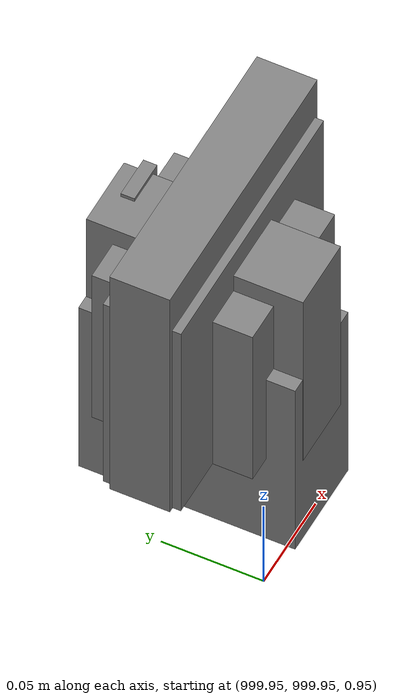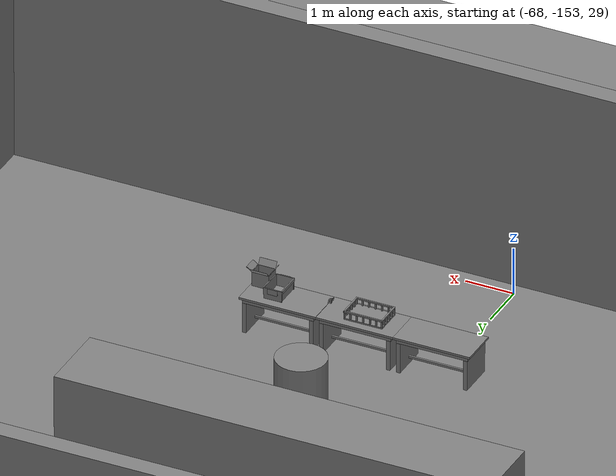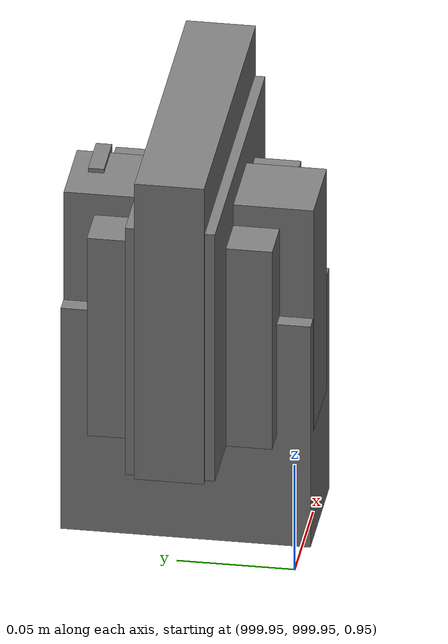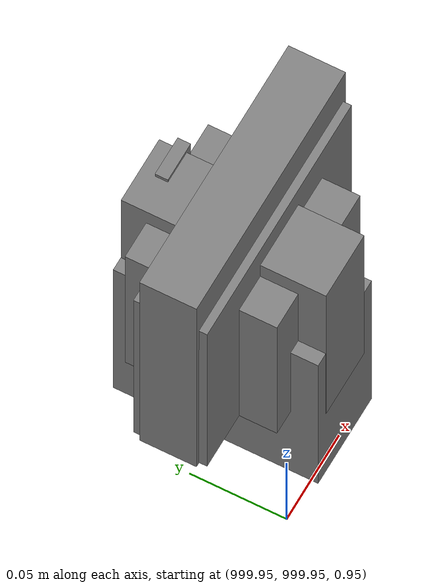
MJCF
<mujoco>
    <option gravity="0.000000000 0.000000000 -9.810000420" timestep="0.0049999999" integrator="implicitfast" density="1.225" viscosity="1.8000001e-05" noslip_iterations="10" iterations="100" sdf_iterations="50">
        <flag multiccd="disable"/>
    </option>
    <size memory="1000M"/>
    <compiler coordinate="local"/>
    <worldbody>
        <light cutoff="30" pos="0 1 1" dir="0 -1 -2"/>
        <light cutoff="30" pos="0 -1 1" dir="0 1 -2"/>
        <body pos="1000.000000000 1000.000000000 1.000000000" euler="0.000000000 0.000000000 180.000000000" name="openloong_gripper_2f85_fix_base_usda_cpu_fan">
            <geom contype="1" conaffinity="1" density="1000" type="box" material="" rgba="0.500000000 0.500000000 0.500000000 1.000000000" solimp="0.899999976 0.949999988 0.001000000" friction="1.000000000 0.005000000 0.000100000" solref="0.020000000 1.000000000" margin="0" condim="3" group="0" pos="0.000000000 0.000000000 0.070034981" quat="0.000000000 0.000000000 0.000000000 1.000000000" size="0.070700005 0.014699999 0.070700005" name="openloong_gripper_2f85_fix_base_usda_geom_A078003A_9F0C_4CC6_A7F8_2DD8769F9803"/>
            <freejoint name="openloong_gripper_2f85_fix_base_usda_cpu_fan_joint"/>
            <site size="0.005000000 0.005000000 0.005000000" rgba="0.500000000 0.500000000 0.500000000 1.000000000" pos="0.000000000 0.000000000 0.000000000" quat="0.999961913 0.008726535 0.000000000 0.000000000" group="0" type="sphere" name="openloong_gripper_2f85_fix_base_usda_cpu_fancsite"/>
        </body>
        <body pos="1000.000000000 1000.000000000 1.000000000" euler="0.000011953 0.000005123 -179.999984741" name="openloong_gripper_2f85_fix_base_usda_intel_box">
            <geom contype="1" conaffinity="1" density="1000" type="box" material="" rgba="0.500000000 0.500000000 0.500000000 1.000000000" solimp="0.899999976 0.949999988 0.001000000" friction="1.000000000 0.005000000 0.000100000" solref="0.020000000 1.000000000" margin="0" condim="3" group="0" pos="0.000000000 -0.000067139 0.000082284" quat="0.707106709 0.000000225 0.000000253 0.707106650" size="0.052800003 0.025300000 0.052800003" name="openloong_gripper_2f85_fix_base_usda_geom_6C521B0E_98F0_4862_AC0C_D2E0C4A17EC6"/>
            <freejoint name="openloong_gripper_2f85_fix_base_usda_intel_box_joint"/>
            <site size="0.005000000 0.005000000 0.005000000" rgba="0.500000000 0.500000000 0.500000000 1.000000000" pos="0.000000000 0.000000000 0.000000000" quat="0.999961913 0.008726500 0.000000000 0.000000000" group="0" type="sphere" name="openloong_gripper_2f85_fix_base_usda_intel_boxsite"/>
        </body>
        <body pos="-66.283691406 -149.409851074 31.163284302" euler="153.051040649 -12.758287430 60.952056885" mocap="true" name="spotlight1_SpotLight"/>
        <body pos="-65.834991455 -149.452560425 31.171548843" euler="85.568099976 -16.637701035 -32.179546356" mocap="true" name="spotlight6_SpotLight"/>
        <body pos="1000.000000000 1000.000000000 1.000000000" euler="0.000000000 0.000000000 180.000000000" name="openloong_gripper_2f85_fix_base_usda_wifi_box">
            <geom contype="1" conaffinity="1" density="1000" type="box" material="" rgba="0.500000000 0.500000000 0.500000000 1.000000000" solimp="0.899999976 0.949999988 0.001000000" friction="1.000000000 0.005000000 0.000100000" solref="0.020000000 1.000000000" margin="0" condim="3" group="0" pos="0.000000000 0.000000000 0.058978677" quat="0.000000000 0.000000047 0.000000000 1.000000000" size="0.068499997 0.018999999 0.059000000" name="openloong_gripper_2f85_fix_base_usda_geom_394BB08C_E072_4DF9_A08D_F83D38B0EA98"/>
            <freejoint name="openloong_gripper_2f85_fix_base_usda_wifi_box_joint"/>
            <site size="0.005000000 0.005000000 0.005000000" rgba="0.500000000 0.500000000 0.500000000 1.000000000" pos="0.000000000 0.000000000 0.000000000" quat="0.999961913 0.008726500 0.000000000 0.000000000" group="0" type="sphere" name="openloong_gripper_2f85_fix_base_usda_wifi_boxsite"/>
        </body>
        <body pos="1000.000000000 999.999938965 1.000000000" euler="0.000000000 0.000000000 180.000000000" name="openloong_gripper_2f85_fix_base_usda_intelcore_i5">
            <geom contype="1" conaffinity="1" density="1000" type="box" material="" rgba="0.500000000 0.500000000 0.500000000 1.000000000" solimp="0.899999976 0.949999988 0.001000000" friction="1.000000000 0.005000000 0.000100000" solref="0.020000000 1.000000000" margin="0" condim="3" group="0" pos="0.000000000 0.000000000 0.051722717" quat="0.707106709 0.000000000 0.000000000 -0.707106769" size="0.052800000 0.018080002 0.052800000" name="openloong_gripper_2f85_fix_base_usda_geom_E14A24B6_9986_4B0F_AE3B_635AE301E605"/>
            <freejoint name="openloong_gripper_2f85_fix_base_usda_intelcore_i5_joint"/>
            <site size="0.005000000 0.005000000 0.005000000" rgba="0.500000000 0.500000000 0.500000000 1.000000000" pos="0.000000000 0.000000000 0.000000000" quat="0.999961913 0.008726534 0.000000000 0.000000000" group="0" type="sphere" name="openloong_gripper_2f85_fix_base_usda_intelcore_i5site"/>
        </body>
        <body pos="-66.017707825 -149.441375732 31.171852112" euler="-153.732925415 -10.541392326 -131.752975464" mocap="true" name="spotlight3_SpotLight"/>
        <body pos="1000.000000000 1000.000000000 1.000000000" euler="0.000000000 0.000000000 180.000000000" name="openloong_gripper_2f85_fix_base_usda_battery_01">
            <geom contype="1" conaffinity="1" density="1000" type="box" material="" rgba="0.500000000 0.500000000 0.500000000 1.000000000" solimp="0.899999976 0.949999988 0.001000000" friction="1.000000000 0.005000000 0.000100000" solref="0.020000000 1.000000000" margin="0" condim="3" group="0" pos="-0.011123657 -0.041940309 0.101691343" quat="1.000000000 0.000000000 0.000000000 0.000000000" size="0.010800000 0.003375000 0.004725000" name="openloong_gripper_2f85_fix_base_usda_geom_7AB01ABD_E138_4FCC_8BAE_C28947FD5536"/>
            <geom contype="1" conaffinity="1" density="1000" type="box" material="" rgba="0.500000000 0.500000000 0.500000000 1.000000000" solimp="0.899999976 0.949999988 0.001000000" friction="1.000000000 0.005000000 0.000100000" solref="0.020000000 1.000000000" margin="0" condim="3" group="0" pos="-0.010876465 -0.044247437 0.047066893" quat="0.998702705 -0.050920475 0.000000000 0.000000000" size="0.009450001 0.002700000 0.024975000" name="openloong_gripper_2f85_fix_base_usda_geom_8207E75B_9C12_4F72_BE1F_18DD3BCE1E41"/>
            <geom contype="1" conaffinity="1" density="1000" type="box" material="" rgba="0.500000000 0.500000000 0.500000000 1.000000000" solimp="0.899999976 0.949999988 0.001000000" friction="1.000000000 0.005000000 0.000100000" solref="0.020000000 1.000000000" margin="0" condim="3" group="0" pos="-0.001235962 -0.000659180 0.047381196" quat="1.000000000 0.000000000 0.000000000 0.000000000" size="0.039420001 0.039150000 0.047250003" name="openloong_gripper_2f85_fix_base_usda_geom_3AB09C03_6E66_4C72_BD3F_734190910F3E"/>
            <geom contype="1" conaffinity="1" density="1000" type="box" material="" rgba="0.500000000 0.500000000 0.500000000 1.000000000" solimp="0.899999976 0.949999988 0.001000000" friction="1.000000000 0.005000000 0.000100000" solref="0.020000000 1.000000000" margin="0" condim="3" group="0" pos="-0.010876465 -0.039138794 0.009851727" quat="1.000000000 0.000000000 0.000000000 0.000000000" size="0.009450001 0.010800000 0.013500000" name="openloong_gripper_2f85_fix_base_usda_geom_EF918DEC_57A0_4963_A2A1_4A26D1E99AE5"/>
            <geom contype="1" conaffinity="1" density="1000" type="box" material="" rgba="0.500000000 0.500000000 0.500000000 1.000000000" solimp="0.899999976 0.949999988 0.001000000" friction="1.000000000 0.005000000 0.000100000" solref="0.020000000 1.000000000" margin="0" condim="3" group="0" pos="-0.010876465 -0.041528322 0.071508206" quat="1.000000000 0.000000000 0.000000000 0.000000000" size="0.009450001 0.002700000 0.027000001" name="openloong_gripper_2f85_fix_base_usda_geom_CD30A4EE_FA07_4073_AD91_8B8F6A8CA70B"/>
            <freejoint name="openloong_gripper_2f85_fix_base_usda_battery_01_joint"/>
            <site size="0.005000000 0.005000000 0.005000000" rgba="0.500000000 0.500000000 0.500000000 1.000000000" pos="0.000000000 0.000000000 0.000000000" quat="0.999961913 0.008726500 0.000000000 0.000000000" group="0" type="sphere" name="openloong_gripper_2f85_fix_base_usda_battery_01site"/>
        </body>
        <body pos="-64.866622925 -149.383972168 30.183746338" euler="89.999984741 89.999946594 0.000000000" name="openloong_gripper_2f85_fix_base_usda_bluebox_01">
            <geom contype="1" conaffinity="1" density="1000" type="box" material="" rgba="0.500000000 0.500000000 0.500000000 1.000000000" solimp="0.899999976 0.949999988 0.001000000" friction="1.000000000 0.005000000 0.000100000" solref="0.020000000 1.000000000" margin="0" condim="3" group="0" pos="0.276580811 0.187225342 0.000068665" quat="0.707106948 0.000077471 0.707106352 0.000077486" size="0.100000001 0.057999998 0.010000000" name="openloong_gripper_2f85_fix_base_usda_geom_1D38E013_EC91_4908_8E14_D2547B04DE7D"/>
            <geom contype="1" conaffinity="1" density="1000" type="box" material="" rgba="0.500000000 0.500000000 0.500000000 1.000000000" solimp="0.899999976 0.949999988 0.001000000" friction="1.000000000 0.005000000 0.000100000" solref="0.020000000 1.000000000" margin="0" condim="3" group="0" pos="0.000000000 0.002883911 0.000000000" quat="0.999999881 0.000000000 0.000000000 0.000000000" size="0.254000008 0.003000000 0.172000006" name="openloong_gripper_2f85_fix_base_usda_geom_15C18A93_72E6_4B8F_AE06_EC75C49C29F2"/>
            <geom contype="1" conaffinity="1" density="1000" type="box" material="" rgba="0.500000000 0.500000000 0.500000000 1.000000000" solimp="0.899999976 0.949999988 0.001000000" friction="1.000000000 0.005000000 0.000100000" solref="0.020000000 1.000000000" margin="0" condim="3" group="0" pos="0.000000000 0.124874115 0.173484802" quat="0.999796331 0.020176515 -0.000000015 0.000000030" size="0.259999990 0.119999997 0.007000000" name="openloong_gripper_2f85_fix_base_usda_geom_187CE335_E9B2_42FB_938F_2521680D98F0"/>
            <geom contype="1" conaffinity="1" density="1000" type="box" material="" rgba="0.500000000 0.500000000 0.500000000 1.000000000" solimp="0.899999976 0.949999988 0.001000000" friction="1.000000000 0.005000000 0.000100000" solref="0.020000000 1.000000000" margin="0" condim="3" group="0" pos="0.000000000 0.124874115 -0.173469543" quat="0.999796331 -0.020176545 -0.000000015 0.000000000" size="0.259999990 0.119999997 0.007000000" name="openloong_gripper_2f85_fix_base_usda_geom_EA6878C0_06E9_47CF_A351_224BA4DF4498"/>
            <geom contype="1" conaffinity="1" density="1000" type="box" material="" rgba="0.500000000 0.500000000 0.500000000 1.000000000" solimp="0.899999976 0.949999988 0.001000000" friction="1.000000000 0.005000000 0.000100000" solref="0.020000000 1.000000000" margin="0" condim="3" group="0" pos="0.000000000 0.214008331 0.188980103" quat="0.999912977 0.013176724 0.000000015 0.000000000" size="0.259999990 0.029999999 0.012500000" name="openloong_gripper_2f85_fix_base_usda_geom_EC86B86A_D79D_4D61_A934_BF5B1BA61D3B"/>
            <geom contype="1" conaffinity="1" density="1000" type="box" material="" rgba="0.500000000 0.500000000 0.500000000 1.000000000" solimp="0.899999976 0.949999988 0.001000000" friction="1.000000000 0.005000000 0.000100000" solref="0.020000000 1.000000000" margin="0" condim="3" group="0" pos="-0.258361816 0.125289917 0.001876831" quat="0.702796936 -0.020792112 0.710783124 0.020769298" size="0.189999998 0.119999997 0.009000000" name="openloong_gripper_2f85_fix_base_usda_geom_0D61D29D_0A46_4784_934E_20440D937168"/>
            <geom contype="1" conaffinity="1" density="1000" type="box" material="" rgba="0.500000000 0.500000000 0.500000000 1.000000000" solimp="0.899999976 0.949999988 0.001000000" friction="1.000000000 0.005000000 0.000100000" solref="0.020000000 1.000000000" margin="0" condim="3" group="0" pos="0.000000000 0.214008331 -0.188980103" quat="0.999912977 -0.013176769 0.000000030 0.000000015" size="0.259999990 0.029999999 0.012500000" name="openloong_gripper_2f85_fix_base_usda_geom_F0C5626A_546B_4C36_AFA2_CEBE98CA7644"/>
            <geom contype="1" conaffinity="1" density="1000" type="box" material="" rgba="0.500000000 0.500000000 0.500000000 1.000000000" solimp="0.899999976 0.949999988 0.001000000" friction="1.000000000 0.005000000 0.000100000" solref="0.020000000 1.000000000" margin="0" condim="3" group="0" pos="-0.276611328 0.187225342 0.000068665" quat="0.707106650 0.000077441 0.707106709 0.000077456" size="0.100000001 0.057999998 0.010000000" name="openloong_gripper_2f85_fix_base_usda_geom_33604ABB_E89B_472A_89C6_28FD01532BF1"/>
            <geom contype="1" conaffinity="1" density="1000" type="box" material="" rgba="0.500000000 0.500000000 0.500000000 1.000000000" solimp="0.899999976 0.949999988 0.001000000" friction="1.000000000 0.005000000 0.000100000" solref="0.020000000 1.000000000" margin="0" condim="3" group="0" pos="0.258331299 0.125289917 0.001876831" quat="0.702851415 0.018856421 0.710823774 -0.019329369" size="0.189999998 0.119999997 0.009000000" name="openloong_gripper_2f85_fix_base_usda_geom_6C93149E_2AF9_4C00_81B5_1ABEAE3418DA"/>
            <freejoint name="openloong_gripper_2f85_fix_base_usda_bluebox_01_joint"/>
            <site size="0.005000000 0.005000000 0.005000000" rgba="0.500000000 0.500000000 0.500000000 1.000000000" pos="0.000000000 0.000000000 0.000000000" quat="0.999961913 0.008726534 0.000000000 0.000000000" group="0" type="sphere" name="openloong_gripper_2f85_fix_base_usda_bluebox_01site"/>
        </body>
        <body pos="-64.496299744 -149.491867065 30.235729218" euler="0.000000000 0.000000000 89.999946594" name="openloong_gripper_2f85_fix_base_usda_cardboardbox_01">
            <geom contype="1" conaffinity="1" density="1000" type="box" material="" rgba="0.500000000 0.500000000 0.500000000 1.000000000" solimp="0.899999976 0.949999988 0.001000000" friction="1.000000000 0.005000000 0.000100000" solref="0.020000000 1.000000000" margin="0" condim="3" group="0" pos="-0.003166199 -0.004086494 0.005052090" quat="1.000000000 0.000000000 0.000000000 0.000000000" size="0.142499998 0.177500010 0.005000000" name="openloong_gripper_2f85_fix_base_usda_geom_F571BD70_0F5B_449B_8FC0_CE219C96A486"/>
            <geom contype="1" conaffinity="1" density="1000" type="box" material="" rgba="0.500000000 0.500000000 0.500000000 1.000000000" solimp="0.899999976 0.949999988 0.001000000" friction="1.000000000 0.005000000 0.000100000" solref="0.020000000 1.000000000" margin="0" condim="3" group="0" pos="-0.003166199 0.170316696 0.150570869" quat="1.000000000 0.000000000 0.000000000 0.000000000" size="0.142499998 0.005000000 0.149999991" name="openloong_gripper_2f85_fix_base_usda_geom_75107FDA_5AF9_4021_BE77_B3C2951D810D"/>
            <geom contype="1" conaffinity="1" density="1000" type="box" material="" rgba="0.500000000 0.500000000 0.500000000 1.000000000" solimp="0.899999976 0.949999988 0.001000000" friction="1.000000000 0.005000000 0.000100000" solref="0.020000000 1.000000000" margin="0" condim="3" group="0" pos="-0.147399902 -0.005307198 0.150570869" quat="1.000000000 0.000000000 0.000000000 0.000000000" size="0.005000000 0.177500010 0.149999991" name="openloong_gripper_2f85_fix_base_usda_geom_DE8A7D5F_B086_425D_A561_CA9FD7D7B22C"/>
            <geom contype="1" conaffinity="1" density="1000" type="box" material="" rgba="0.500000000 0.500000000 0.500000000 1.000000000" solimp="0.899999976 0.949999988 0.001000000" friction="1.000000000 0.005000000 0.000100000" solref="0.020000000 1.000000000" margin="0" condim="3" group="0" pos="0.140275955 -0.005307198 0.150570869" quat="1.000000000 0.000000000 0.000000000 0.000000000" size="0.005000000 0.177500010 0.149999991" name="openloong_gripper_2f85_fix_base_usda_geom_2B55986C_F6D3_4924_B75A_5458C8A12EEC"/>
            <geom contype="1" conaffinity="1" density="1000" type="box" material="" rgba="0.500000000 0.500000000 0.500000000 1.000000000" solimp="0.899999976 0.949999988 0.001000000" friction="1.000000000 0.005000000 0.000100000" solref="0.020000000 1.000000000" margin="0" condim="3" group="0" pos="-0.003166199 -0.181550980 0.150570869" quat="1.000000000 0.000000000 0.000000000 0.000000000" size="0.142499998 0.005000000 0.149999991" name="openloong_gripper_2f85_fix_base_usda_geom_7D263C2B_A539_48A2_9374_9EA2FAE8A2E9"/>
            <freejoint name="openloong_gripper_2f85_fix_base_usda_cardboardbox_01_joint"/>
            <site size="0.005000000 0.005000000 0.005000000" rgba="0.500000000 0.500000000 0.500000000 1.000000000" pos="0.000000000 0.000000000 0.000000000" quat="0.999961913 0.008726535 0.000000000 0.000000000" group="0" type="sphere" name="openloong_gripper_2f85_fix_base_usda_site_E60C6472_D14F_41E5_93EF_6E95575073DD"/>
            <body pos="0.139160156 -0.004048347 0.301930904" euler="-179.999954224 49.383502960 179.999954224" name="openloong_gripper_2f85_fix_base_usda_A1_006">
                <geom contype="1" conaffinity="1" density="1000" type="box" material="" rgba="0.500000000 0.500000000 0.500000000 1.000000000" solimp="0.899999976 0.949999988 0.001000000" friction="1.000000000 0.005000000 0.000100000" solref="0.020000000 1.000000000" margin="0" condim="3" group="0" pos="-0.071587563 0.000009537 0.001745224" quat="0.999999881 0.000000000 0.000000000 0.000000000" size="0.071249999 0.179999992 0.002500000" name="openloong_gripper_2f85_fix_base_usda_geom_7CE48ED3_E278_4800_9346_0B2AFA1417EF"/>
                <joint armature="0" stiffness="0.07" damping="0.0099999998" axis="0.000000 1.000000 0.000000" type="hinge" name="openloong_gripper_2f85_fix_base_usda_A1_006"/>
            </body>
            <body pos="-0.145902634 -0.004086494 0.301938057" euler="-180.000000000 -60.000011444 -180.000000000" name="openloong_gripper_2f85_fix_base_usda_A2_006">
                <geom contype="1" conaffinity="1" density="1000" type="box" material="" rgba="0.500000000 0.500000000 0.500000000 1.000000000" solimp="0.899999976 0.949999988 0.001000000" friction="1.000000000 0.005000000 0.000100000" solref="0.020000000 1.000000000" margin="0" condim="3" group="0" pos="0.071268082 0.000009537 0.002717972" quat="0.000002921 0.000000000 -0.000000030 0.999999881" size="0.071249999 0.179999992 0.002500000" name="openloong_gripper_2f85_fix_base_usda_geom_A676351E_801B_43E7_A29C_6AB98CF6256B"/>
                <joint armature="0" stiffness="0.07" damping="0.0099999998" axis="0.000000 1.000000 0.000000" type="hinge" name="openloong_gripper_2f85_fix_base_usda_A2_006"/>
            </body>
            <body pos="-0.003385544 0.175991058 0.301930904" euler="-125.858116150 -0.000004561 0.000002331" name="openloong_gripper_2f85_fix_base_usda_B2_006">
                <geom contype="1" conaffinity="1" density="1000" type="box" material="" rgba="0.500000000 0.500000000 0.500000000 1.000000000" solimp="0.899999976 0.949999988 0.001000000" friction="1.000000000 0.005000000 0.000100000" solref="0.020000000 1.000000000" margin="0" condim="3" group="0" pos="0.000009537 -0.070939064 -0.002470016" quat="0.999614120 0.027776197 -0.000000015 0.000000030" size="0.137500003 0.064999998 0.005000000" name="openloong_gripper_2f85_fix_base_usda_geom_506C4B7E_3E81_47EC_9808_2F8A98B49704"/>
                <joint armature="0" stiffness="0.07" damping="0.0099999998" axis="1.000000 0.000000 0.000000" type="hinge" name="openloong_gripper_2f85_fix_base_usda_B2_006"/>
            </body>
            <body pos="-0.003385544 -0.184140205 0.301938057" euler="147.805557251 0.000000000 0.000000000" name="openloong_gripper_2f85_fix_base_usda_B1_006">
                <geom contype="1" conaffinity="1" density="1000" type="box" material="" rgba="0.500000000 0.500000000 0.500000000 1.000000000" solimp="0.899999976 0.949999988 0.001000000" friction="1.000000000 0.005000000 0.000100000" solref="0.020000000 1.000000000" margin="0" condim="3" group="0" pos="-0.000028610 0.070202351 -0.002703667" quat="0.999614179 -0.027776167 0.000000000 0.000000000" size="0.137500003 0.064999998 0.005000000" name="openloong_gripper_2f85_fix_base_usda_geom_4B57CDA8_925A_48BD_8BC7_5AC1FAE5F342"/>
                <joint armature="0" stiffness="0.07" damping="0.0099999998" axis="1.000000 0.000000 0.000000" type="hinge" name="openloong_gripper_2f85_fix_base_usda_B1_006"/>
            </body>
        </body>
        <body pos="-65.882858276 -149.481979370 30.229999542" euler="-64.487716675 0.000000000 0.000000000" name="openloong_gripper_2f85_fix_base_usda_Barcode">
            <geom contype="1" conaffinity="1" density="1000" type="box" material="" rgba="0.500000000 0.500000000 0.500000000 1.000000000" solimp="0.899999976 0.949999988 0.001000000" friction="1.000000000 0.005000000 0.000100000" solref="0.020000000 1.000000000" margin="0" condim="3" group="0" pos="0.000000000 0.013038635 0.001419067" quat="0.000000000 0.000000000 0.000000000 1.000000119" size="0.034000002 0.010000000 0.017999999" name="openloong_gripper_2f85_fix_base_usda_geom_5AACE668_5E59_4B39_B2EC_5F32F75E006C"/>
            <geom contype="1" conaffinity="1" density="1000" type="box" material="" rgba="0.500000000 0.500000000 0.500000000 1.000000000" solimp="0.899999976 0.949999988 0.001000000" friction="1.000000000 0.005000000 0.000100000" solref="0.020000000 1.000000000" margin="0" condim="3" group="0" pos="0.000000000 -0.035301208 -0.007095337" quat="0.000000000 0.000000000 -0.043619365 0.999048233" size="0.028999999 0.010000000 0.020000000" name="openloong_gripper_2f85_fix_base_usda_geom_D7A18B11_2202_48E2_B47B_3F710BEE02D5"/>
            <geom contype="1" conaffinity="1" density="1000" type="box" material="" rgba="0.500000000 0.500000000 0.500000000 1.000000000" solimp="0.899999976 0.949999988 0.001000000" friction="1.000000000 0.005000000 0.000100000" solref="0.020000000 1.000000000" margin="0" condim="3" group="0" pos="0.000000000 -0.043411255 -0.011749268" quat="0.922262907 0.386563420 0.000000000 0.000000000" size="0.026000001 0.010000000 0.020000000" name="openloong_gripper_2f85_fix_base_usda_geom_C6710796_EC5C_4958_879C_29FB1A6D747D"/>
            <geom contype="1" conaffinity="1" density="1000" type="box" material="" rgba="0.500000000 0.500000000 0.500000000 1.000000000" solimp="0.899999976 0.949999988 0.001000000" friction="1.000000000 0.005000000 0.000100000" solref="0.020000000 1.000000000" margin="0" condim="3" group="0" pos="0.000000000 -0.016967773 -0.031860352" quat="0.000000000 0.000000000 0.000000000 1.000000119" size="0.008000000 0.010000000 0.013000000" name="openloong_gripper_2f85_fix_base_usda_geom_27F50482_D4B5_4F78_8621_9F28F5D00DE4"/>
            <geom contype="1" conaffinity="1" density="1000" type="box" material="" rgba="0.500000000 0.500000000 0.500000000 1.000000000" solimp="0.899999976 0.949999988 0.001000000" friction="1.000000000 0.005000000 0.000100000" solref="0.020000000 1.000000000" margin="0" condim="3" group="0" pos="0.000000000 -0.001869202 0.000312805" quat="0.953716993 0.300705761 0.000000000 0.000000000" size="0.032000002 0.010000000 0.018999999" name="openloong_gripper_2f85_fix_base_usda_geom_5EDF0C3F_C46F_467E_9DBE_6430A879503B"/>
            <geom contype="1" conaffinity="1" density="1000" type="box" material="" rgba="0.500000000 0.500000000 0.500000000 1.000000000" solimp="0.899999976 0.949999988 0.001000000" friction="1.000000000 0.005000000 0.000100000" solref="0.020000000 1.000000000" margin="0" condim="3" group="0" pos="0.000000000 -0.019531250 -0.003173828" quat="0.953716993 0.300705761 0.000000000 0.000000000" size="0.030999999 0.010000000 0.020000000" name="openloong_gripper_2f85_fix_base_usda_geom_5E8D0D58_AD2A_46CF_9ECF_B98215745C9C"/>
            <geom contype="1" conaffinity="1" density="1000" type="box" material="" rgba="0.500000000 0.500000000 0.500000000 1.000000000" solimp="0.899999976 0.949999988 0.001000000" friction="1.000000000 0.005000000 0.000100000" solref="0.020000000 1.000000000" margin="0" condim="3" group="0" pos="0.000000000 -0.035301208 -0.007095337" quat="0.953716993 0.300705761 0.000000000 0.000000000" size="0.028999999 0.010000000 0.020000000" name="openloong_gripper_2f85_fix_base_usda_geom_C25C1AFA_E358_48E3_8FCD_CA48D77D66CB"/>
            <geom contype="1" conaffinity="1" density="1000" type="box" material="" rgba="0.500000000 0.500000000 0.500000000 1.000000000" solimp="0.899999976 0.949999988 0.001000000" friction="1.000000000 0.005000000 0.000100000" solref="0.020000000 1.000000000" margin="0" condim="3" group="0" pos="0.000000000 -0.042617798 -0.071121216" quat="0.000000000 0.000000000 0.000000000 1.000000119" size="0.013000000 0.021000000 0.059999999" name="openloong_gripper_2f85_fix_base_usda_geom_21076255_D29C_4680_A428_2E0DB506E2A8"/>
            <freejoint name="openloong_gripper_2f85_fix_base_usda_Barcode_joint"/>
            <site size="0.005000000 0.005000000 0.005000000" rgba="0.500000000 0.500000000 0.500000000 1.000000000" pos="0.000000000 0.000000000 0.000000000" quat="1.000000000 0.000000000 0.000000000 0.000000000" group="0" type="sphere" name="openloong_gripper_2f85_fix_base_usda_Barcode_site"/>
        </body>
        <body pos="-66.745018005 -149.392349243 30.184000015" euler="0.000000000 0.000000000 89.999946594" name="[22332679143646]_Basket_01">
            <geom contype="1" conaffinity="1" density="1000" type="box" material="" rgba="0.500000000 0.500000000 0.500000000 1.000000000" solimp="0.899999976 0.949999988 0.001000000" friction="1.000000000 0.005000000 0.000100000" solref="0.020000000 1.000000000" margin="0" condim="3" group="0" pos="-0.052425385 0.389207840 0.089787483" quat="0.707107008 0.000000000 0.000000000 0.707106411" size="0.014249999 0.014249999 0.059999999" name="[22332679143646]_geom_7F6F52EF_A5A3_473C_8B2D_866DCD824310"/>
            <geom contype="1" conaffinity="1" density="1000" type="box" material="" rgba="0.500000000 0.500000000 0.500000000 1.000000000" solimp="0.899999976 0.949999988 0.001000000" friction="1.000000000 0.005000000 0.000100000" solref="0.020000000 1.000000000" margin="0" condim="3" group="0" pos="0.264015198 -0.133043289 0.089787483" quat="0.707107008 0.000000000 0.000000000 0.707106411" size="0.014249999 0.014249999 0.059999999" name="[22332679143646]_geom_774E7486_8592_4526_96C4_6B9DA1A5786F"/>
            <geom contype="1" conaffinity="1" density="1000" type="box" material="" rgba="0.500000000 0.500000000 0.500000000 1.000000000" solimp="0.899999976 0.949999988 0.001000000" friction="1.000000000 0.005000000 0.000100000" solref="0.020000000 1.000000000" margin="0" condim="3" group="0" pos="-0.264015198 -0.265548706 0.089793205" quat="0.707107008 0.000000000 0.000000000 0.707106411" size="0.014249999 0.014249999 0.059999999" name="[22332679143646]_geom_860DD5E0_554F_49B5_A6A7_5C27FB8DD9D0"/>
            <geom contype="1" conaffinity="1" density="1000" type="box" material="" rgba="0.500000000 0.500000000 0.500000000 1.000000000" solimp="0.899999976 0.949999988 0.001000000" friction="1.000000000 0.005000000 0.000100000" solref="0.020000000 1.000000000" margin="0" condim="3" group="0" pos="-0.160263062 -0.389322281 0.089793205" quat="0.707107008 0.000000000 0.000000000 0.707106411" size="0.014249999 0.014249999 0.059999999" name="[22332679143646]_geom_175BE10D_7BC8_4C6A_BD50_DF61082DEACD"/>
            <geom contype="1" conaffinity="1" density="1000" type="box" material="" rgba="0.500000000 0.500000000 0.500000000 1.000000000" solimp="0.899999976 0.949999988 0.001000000" friction="1.000000000 0.005000000 0.000100000" solref="0.020000000 1.000000000" margin="0" condim="3" group="0" pos="0.162265778 -0.389322281 0.089787483" quat="0.707107008 0.000000000 0.000000000 0.707106411" size="0.014249999 0.014249999 0.059999999" name="[22332679143646]_geom_02D5FFB5_7444_40FF_9AF4_E4B9D54462B2"/>
            <geom contype="1" conaffinity="1" density="1000" type="box" material="" rgba="0.500000000 0.500000000 0.500000000 1.000000000" solimp="0.899999976 0.949999988 0.001000000" friction="1.000000000 0.005000000 0.000100000" solref="0.020000000 1.000000000" margin="0" condim="3" group="0" pos="0.264015198 0.389207840 0.089787483" quat="0.707107008 0.000000000 0.000000000 0.707106411" size="0.014249999 0.014249999 0.059999999" name="[22332679143646]_geom_782D4B24_7D86_4883_9EA5_596F4FB50423"/>
            <geom contype="1" conaffinity="1" density="1000" type="box" material="" rgba="0.500000000 0.500000000 0.500000000 1.000000000" solimp="0.899999976 0.949999988 0.001000000" friction="1.000000000 0.005000000 0.000100000" solref="0.020000000 1.000000000" margin="0" condim="3" group="0" pos="-0.264015198 -0.133043289 0.089793205" quat="0.707107008 0.000000000 0.000000000 0.707106411" size="0.014249999 0.014249999 0.059999999" name="[22332679143646]_geom_0DC4BE49_50BE_42E2_938E_3060B96BA7F5"/>
            <geom contype="1" conaffinity="1" density="1000" type="box" material="" rgba="0.500000000 0.500000000 0.500000000 1.000000000" solimp="0.899999976 0.949999988 0.001000000" friction="1.000000000 0.005000000 0.000100000" solref="0.020000000 1.000000000" margin="0" condim="3" group="0" pos="-0.264026642 0.269256592 0.089793205" quat="0.707107008 0.000000000 0.000000000 0.707106411" size="0.014249999 0.014249999 0.059999999" name="[22332679143646]_geom_DA2BD4F8_E722_4BE9_B3EC_3FF0CBE9D122"/>
            <geom contype="1" conaffinity="1" density="1000" type="box" material="" rgba="0.500000000 0.500000000 0.500000000 1.000000000" solimp="0.899999976 0.949999988 0.001000000" friction="1.000000000 0.005000000 0.000100000" solref="0.020000000 1.000000000" margin="0" condim="3" group="0" pos="0.054462433 0.389207840 0.089787483" quat="0.707107008 0.000000000 0.000000000 0.707106411" size="0.014249999 0.014249999 0.059999999" name="[22332679143646]_geom_67DE76D4_7EEC_42B1_BD85_6A9B3E757DE3"/>
            <geom contype="1" conaffinity="1" density="1000" type="box" material="" rgba="0.500000000 0.500000000 0.500000000 1.000000000" solimp="0.899999976 0.949999988 0.001000000" friction="1.000000000 0.005000000 0.000100000" solref="0.020000000 1.000000000" margin="0" condim="3" group="0" pos="0.054462433 -0.389322281 0.089787483" quat="0.707107008 0.000000000 0.000000000 0.707106411" size="0.014249999 0.014249999 0.059999999" name="[22332679143646]_geom_DFA1E14A_0E2B_4B3F_B324_BB248E697EDC"/>
            <geom contype="1" conaffinity="1" density="1000" type="box" material="" rgba="0.500000000 0.500000000 0.500000000 1.000000000" solimp="0.899999976 0.949999988 0.001000000" friction="1.000000000 0.005000000 0.000100000" solref="0.020000000 1.000000000" margin="0" condim="3" group="0" pos="0.264015198 0.269256592 0.089793205" quat="0.707107008 0.000000000 0.000000000 0.707106411" size="0.014249999 0.014249999 0.059999999" name="[22332679143646]_geom_BFBD49D7_1BB8_4EDC_B542_FC88673EC386"/>
            <geom contype="1" conaffinity="1" density="1000" type="box" material="" rgba="0.500000000 0.500000000 0.500000000 1.000000000" solimp="0.899999976 0.949999988 0.001000000" friction="1.000000000 0.005000000 0.000100000" solref="0.020000000 1.000000000" margin="0" condim="3" group="0" pos="0.264015198 -0.389322281 0.089787483" quat="0.707107008 0.000000000 0.000000000 0.707106411" size="0.014249999 0.014249999 0.059999999" name="[22332679143646]_geom_6F62FDF0_2DE3_42CC_BEEA_29F5F13AFC89"/>
            <geom contype="1" conaffinity="1" density="1000" type="box" material="" rgba="0.500000000 0.500000000 0.500000000 1.000000000" solimp="0.899999976 0.949999988 0.001000000" friction="1.000000000 0.005000000 0.000100000" solref="0.020000000 1.000000000" margin="0" condim="3" group="0" pos="0.000000000 0.000000000 0.015998840" quat="0.707107008 0.000000000 0.000000000 0.707106411" size="0.403499991 0.279000014 0.015750000" name="[22332679143646]_geom_ADDDE40E_F941_4DD6_8C03_E69B2B4BF6BE"/>
            <geom contype="1" conaffinity="1" density="1000" type="box" material="" rgba="0.500000000 0.500000000 0.500000000 1.000000000" solimp="0.899999976 0.949999988 0.001000000" friction="1.000000000 0.005000000 0.000100000" solref="0.020000000 1.000000000" margin="0" condim="3" group="0" pos="0.000000000 -0.389476776 0.163619041" quat="0.707107008 0.000000000 0.000000000 0.707106411" size="0.015000000 0.277500004 0.015750000" name="[22332679143646]_geom_75806A84_273D_4701_B139_7DFC0DB7D872"/>
            <geom contype="1" conaffinity="1" density="1000" type="box" material="" rgba="0.500000000 0.500000000 0.500000000 1.000000000" solimp="0.899999976 0.949999988 0.001000000" friction="1.000000000 0.005000000 0.000100000" solref="0.020000000 1.000000000" margin="0" condim="3" group="0" pos="0.162265778 0.389207840 0.089787483" quat="0.707107008 0.000000000 0.000000000 0.707106411" size="0.014249999 0.014249999 0.059999999" name="[22332679143646]_geom_97B9F1B9_07BA_4E7B_8F12_63B36494FFC1"/>
            <geom contype="1" conaffinity="1" density="1000" type="box" material="" rgba="0.500000000 0.500000000 0.500000000 1.000000000" solimp="0.899999976 0.949999988 0.001000000" friction="1.000000000 0.005000000 0.000100000" solref="0.020000000 1.000000000" margin="0" condim="3" group="0" pos="0.000000000 0.389471054 0.163619041" quat="0.707107008 0.000000000 0.000000000 0.707106411" size="0.015000000 0.277500004 0.015750000" name="[22332679143646]_geom_65EA2C74_7D5E_4EC3_B0B3_CF1240B512FC"/>
            <geom contype="1" conaffinity="1" density="1000" type="box" material="" rgba="0.500000000 0.500000000 0.500000000 1.000000000" solimp="0.899999976 0.949999988 0.001000000" friction="1.000000000 0.005000000 0.000100000" solref="0.020000000 1.000000000" margin="0" condim="3" group="0" pos="-0.263511658 0.000000000 0.163619041" quat="0.707107008 0.000000000 0.000000000 0.707106411" size="0.403499991 0.015000000 0.015750000" name="[22332679143646]_geom_AEFFB11D_1F9D_4899_817A_5DDBDC3F3D41"/>
            <geom contype="1" conaffinity="1" density="1000" type="box" material="" rgba="0.500000000 0.500000000 0.500000000 1.000000000" solimp="0.899999976 0.949999988 0.001000000" friction="1.000000000 0.005000000 0.000100000" solref="0.020000000 1.000000000" margin="0" condim="3" group="0" pos="-0.264015198 0.141334534 0.089793205" quat="0.707107008 0.000000000 0.000000000 0.707106411" size="0.014249999 0.014249999 0.059999999" name="[22332679143646]_geom_7D4D2378_91F2_43D9_9836_4B7A0EF2F1FB"/>
            <geom contype="1" conaffinity="1" density="1000" type="box" material="" rgba="0.500000000 0.500000000 0.500000000 1.000000000" solimp="0.899999976 0.949999988 0.001000000" friction="1.000000000 0.005000000 0.000100000" solref="0.020000000 1.000000000" margin="0" condim="3" group="0" pos="0.264015198 -0.265548706 0.089787483" quat="0.707107008 0.000000000 0.000000000 0.707106411" size="0.014249999 0.014249999 0.059999999" name="[22332679143646]_geom_A6E81EE1_79B7_4BF3_8BCA_FDD3C6491D6E"/>
            <geom contype="1" conaffinity="1" density="1000" type="box" material="" rgba="0.500000000 0.500000000 0.500000000 1.000000000" solimp="0.899999976 0.949999988 0.001000000" friction="1.000000000 0.005000000 0.000100000" solref="0.020000000 1.000000000" margin="0" condim="3" group="0" pos="-0.160263062 0.389207840 0.089787483" quat="0.707107008 0.000000000 0.000000000 0.707106411" size="0.014249999 0.014249999 0.059999999" name="[22332679143646]_geom_7161FC06_D387_44E8_953D_9F717B1FDE01"/>
            <geom contype="1" conaffinity="1" density="1000" type="box" material="" rgba="0.500000000 0.500000000 0.500000000 1.000000000" solimp="0.899999976 0.949999988 0.001000000" friction="1.000000000 0.005000000 0.000100000" solref="0.020000000 1.000000000" margin="0" condim="3" group="0" pos="-0.052425385 -0.389322281 0.089787483" quat="0.707107008 0.000000000 0.000000000 0.707106411" size="0.014249999 0.014249999 0.059999999" name="[22332679143646]_geom_2CC55755_726C_45D2_9B58_C3CDA98E95C3"/>
            <geom contype="1" conaffinity="1" density="1000" type="box" material="" rgba="0.500000000 0.500000000 0.500000000 1.000000000" solimp="0.899999976 0.949999988 0.001000000" friction="1.000000000 0.005000000 0.000100000" solref="0.020000000 1.000000000" margin="0" condim="3" group="0" pos="-0.264026642 -0.389322281 0.089793205" quat="0.707107008 0.000000000 0.000000000 0.707106411" size="0.014249999 0.014249999 0.059999999" name="[22332679143646]_geom_17C576D5_1FE7_40D9_84E2_729C6E135F7A"/>
            <geom contype="1" conaffinity="1" density="1000" type="box" material="" rgba="0.500000000 0.500000000 0.500000000 1.000000000" solimp="0.899999976 0.949999988 0.001000000" friction="1.000000000 0.005000000 0.000100000" solref="0.020000000 1.000000000" margin="0" condim="3" group="0" pos="0.264015198 0.141334534 0.089787483" quat="0.707107008 0.000000000 0.000000000 0.707106411" size="0.014249999 0.014249999 0.059999999" name="[22332679143646]_geom_25915401_0A6C_4DC2_AA56_69EE0C676678"/>
            <geom contype="1" conaffinity="1" density="1000" type="box" material="" rgba="0.500000000 0.500000000 0.500000000 1.000000000" solimp="0.899999976 0.949999988 0.001000000" friction="1.000000000 0.005000000 0.000100000" solref="0.020000000 1.000000000" margin="0" condim="3" group="0" pos="-0.264015198 0.389207840 0.089793205" quat="0.707107008 0.000000000 0.000000000 0.707106411" size="0.014249999 0.014249999 0.059999999" name="[22332679143646]_geom_0CE52FAC_4706_4561_9933_83F5F6580795"/>
            <geom contype="1" conaffinity="1" density="1000" type="box" material="" rgba="0.500000000 0.500000000 0.500000000 1.000000000" solimp="0.899999976 0.949999988 0.001000000" friction="1.000000000 0.005000000 0.000100000" solref="0.020000000 1.000000000" margin="0" condim="3" group="0" pos="0.264015198 0.004480362 0.089787483" quat="0.707107008 0.000000000 0.000000000 0.707106411" size="0.014249999 0.014249999 0.059999999" name="[22332679143646]_geom_1FC8B801_9241_49BA_9BD0_AF29936BB54C"/>
            <geom contype="1" conaffinity="1" density="1000" type="box" material="" rgba="0.500000000 0.500000000 0.500000000 1.000000000" solimp="0.899999976 0.949999988 0.001000000" friction="1.000000000 0.005000000 0.000100000" solref="0.020000000 1.000000000" margin="0" condim="3" group="0" pos="0.263694763 -0.000011444 0.163619041" quat="0.707107008 0.000000000 0.000000000 0.707106411" size="0.403499991 0.015000000 0.015750000" name="[22332679143646]_geom_AE3EDF97_8A39_43FE_AE62_1D62858D64E1"/>
            <geom contype="1" conaffinity="1" density="1000" type="box" material="" rgba="0.500000000 0.500000000 0.500000000 1.000000000" solimp="0.899999976 0.949999988 0.001000000" friction="1.000000000 0.005000000 0.000100000" solref="0.020000000 1.000000000" margin="0" condim="3" group="0" pos="-0.264015198 0.004480362 0.089793205" quat="0.707107008 0.000000000 0.000000000 0.707106411" size="0.014249999 0.014249999 0.059999999" name="[22332679143646]_geom_12916C4F_F936_4F50_887E_BFC26DA5396C"/>
            <freejoint name="[22332679143646]_joint_95C675D6_0A7F_47D0_959B_F91721627F5A"/>
        </body>
        <body pos="0.000000000 0.000000000 0.000000000" euler="0.000000000 0.000000000 0.000000000" name="Static Objects_Static Objects">
            <geom contype="1" conaffinity="1" density="1000" type="box" material="" rgba="0.500000000 0.500000000 0.500000000 1.000000000" solimp="0.899999976 0.949999988 0.001000000" friction="1.000000000 0.005000000 0.000100000" solref="0.020000000 1.000000000" margin="0" condim="3" group="0" pos="-67.544113159 -149.365814209 29.727830887" quat="0.500000417 0.499999970 0.499999553 0.499999970" size="0.381000012 0.319999993 0.041000001" name="Static Objects_geom_8A0942B1_5E90_4A9D_AA0B_C7260F22782C"/>
            <geom contype="1" conaffinity="1" density="1000" type="box" material="" rgba="0.500000000 0.500000000 0.500000000 1.000000000" solimp="0.899999976 0.949999988 0.001000000" friction="1.000000000 0.005000000 0.000100000" solref="0.020000000 1.000000000" margin="0" condim="3" group="0" pos="-68.239501953 -149.365814209 30.086868286" quat="0.500000417 0.499999970 0.499999553 0.499999970" size="0.370999992 0.039500002 0.745000005" name="Static Objects_geom_3CF6E8E8_F049_4934_B47A_6BB5C870E698"/>
            <geom contype="1" conaffinity="1" density="1000" type="box" material="" rgba="0.500000000 0.500000000 0.500000000 1.000000000" solimp="0.899999976 0.949999988 0.001000000" friction="1.000000000 0.005000000 0.000100000" solref="0.020000000 1.000000000" margin="0" condim="3" group="0" pos="-68.239501953 -149.365814209 30.147235870" quat="0.500000417 0.499999970 0.499999553 0.499999970" size="0.400000006 0.022000000 0.800000012" name="Static Objects_geom_31674AE5_3157_4E26_B782_68A04808E9C6"/>
            <geom contype="1" conaffinity="1" density="1000" type="box" material="" rgba="0.500000000 0.500000000 0.500000000 1.000000000" solimp="0.899999976 0.949999988 0.001000000" friction="1.000000000 0.005000000 0.000100000" solref="0.020000000 1.000000000" margin="0" condim="3" group="0" pos="-68.934890747 -149.365814209 29.727830887" quat="0.500000417 0.499999970 0.499999553 0.499999970" size="0.381000012 0.319999993 0.041000001" name="Static Objects_geom_6A41D9D1_D7D0_4F96_9547_4F4D210378D0"/>
            <geom contype="1" conaffinity="1" density="1000" type="box" material="" rgba="0.500000000 0.500000000 0.500000000 1.000000000" solimp="0.899999976 0.949999988 0.001000000" friction="1.000000000 0.005000000 0.000100000" solref="0.020000000 1.000000000" margin="0" condim="3" group="0" pos="-68.239501953 -149.365814209 29.561563492" quat="0.500000417 0.499999970 0.499999553 0.499999970" size="0.020000000 0.022000000 0.660000026" name="Static Objects_geom_6EAB40BC_831B_432C_B980_4DBD45EE3245"/>
            <geom contype="1" conaffinity="1" density="1000" type="box" material="" rgba="0.500000000 0.500000000 0.500000000 1.000000000" solimp="0.899999976 0.949999988 0.001000000" friction="1.000000000 0.005000000 0.000100000" solref="0.020000000 1.000000000" margin="0" condim="3" group="0" pos="-65.945671082 -149.365814209 29.727830887" quat="0.500000417 0.499999970 0.499999553 0.499999970" size="0.381000012 0.319999993 0.041000001" name="Static Objects_geom_5CF2FD66_FED1_4F6B_A800_DA898E576982"/>
            <geom contype="1" conaffinity="1" density="1000" type="box" material="" rgba="0.500000000 0.500000000 0.500000000 1.000000000" solimp="0.899999976 0.949999988 0.001000000" friction="1.000000000 0.005000000 0.000100000" solref="0.020000000 1.000000000" margin="0" condim="3" group="0" pos="-66.641059875 -149.365814209 30.086868286" quat="0.500000417 0.499999970 0.499999553 0.499999970" size="0.370999992 0.039500002 0.745000005" name="Static Objects_geom_92EE5B01_6469_4810_B3B9_5765BA96F809"/>
            <geom contype="1" conaffinity="1" density="1000" type="box" material="" rgba="0.500000000 0.500000000 0.500000000 1.000000000" solimp="0.899999976 0.949999988 0.001000000" friction="1.000000000 0.005000000 0.000100000" solref="0.020000000 1.000000000" margin="0" condim="3" group="0" pos="-66.641059875 -149.365814209 30.147235870" quat="0.500000417 0.499999970 0.499999553 0.499999970" size="0.400000006 0.022000000 0.800000012" name="Static Objects_geom_697357D0_E468_4FB9_9B4E_AD08053FB6F5"/>
            <geom contype="1" conaffinity="1" density="1000" type="box" material="" rgba="0.500000000 0.500000000 0.500000000 1.000000000" solimp="0.899999976 0.949999988 0.001000000" friction="1.000000000 0.005000000 0.000100000" solref="0.020000000 1.000000000" margin="0" condim="3" group="0" pos="-67.336448669 -149.365814209 29.727830887" quat="0.500000417 0.499999970 0.499999553 0.499999970" size="0.381000012 0.319999993 0.041000001" name="Static Objects_geom_F568B7B1_7FB7_4C75_B9EE_28A277D1977C"/>
            <geom contype="1" conaffinity="1" density="1000" type="box" material="" rgba="0.500000000 0.500000000 0.500000000 1.000000000" solimp="0.899999976 0.949999988 0.001000000" friction="1.000000000 0.005000000 0.000100000" solref="0.020000000 1.000000000" margin="0" condim="3" group="0" pos="-66.641059875 -149.365814209 29.561563492" quat="0.500000417 0.499999970 0.499999553 0.499999970" size="0.020000000 0.022000000 0.660000026" name="Static Objects_geom_71B79523_3FC1_4611_BC1C_1A4E3CB51380"/>
            <geom contype="1" conaffinity="1" density="1000" type="box" material="" rgba="0.500000000 0.500000000 0.500000000 1.000000000" solimp="0.899999976 0.949999988 0.001000000" friction="1.000000000 0.005000000 0.000100000" solref="0.020000000 1.000000000" margin="0" condim="3" group="0" pos="-64.338577271 -149.365814209 29.727830887" quat="0.500000417 0.499999970 0.499999553 0.499999970" size="0.381000012 0.319999993 0.041000001" name="Static Objects_geom_2B73BEE4_1CB6_4E8A_815A_BB18586C0A07"/>
            <geom contype="1" conaffinity="1" density="1000" type="box" material="" rgba="0.500000000 0.500000000 0.500000000 1.000000000" solimp="0.899999976 0.949999988 0.001000000" friction="1.000000000 0.005000000 0.000100000" solref="0.020000000 1.000000000" margin="0" condim="3" group="0" pos="-65.033966064 -149.365814209 30.086868286" quat="0.500000417 0.499999970 0.499999553 0.499999970" size="0.370999992 0.039500002 0.745000005" name="Static Objects_geom_96369AAE_3F7A_4377_9E2F_3E98341B6EF4"/>
            <geom contype="1" conaffinity="1" density="1000" type="box" material="" rgba="0.500000000 0.500000000 0.500000000 1.000000000" solimp="0.899999976 0.949999988 0.001000000" friction="1.000000000 0.005000000 0.000100000" solref="0.020000000 1.000000000" margin="0" condim="3" group="0" pos="-65.033966064 -149.365814209 30.147235870" quat="0.500000417 0.499999970 0.499999553 0.499999970" size="0.400000006 0.022000000 0.800000012" name="Static Objects_geom_1CCCB5AE_2688_4F36_A910_140065E5DB4E"/>
            <geom contype="1" conaffinity="1" density="1000" type="box" material="" rgba="0.500000000 0.500000000 0.500000000 1.000000000" solimp="0.899999976 0.949999988 0.001000000" friction="1.000000000 0.005000000 0.000100000" solref="0.020000000 1.000000000" margin="0" condim="3" group="0" pos="-65.729354858 -149.365814209 29.727830887" quat="0.500000417 0.499999970 0.499999553 0.499999970" size="0.381000012 0.319999993 0.041000001" name="Static Objects_geom_1FD3136D_7356_4A44_B4BF_8D0B6C6FF116"/>
            <geom contype="1" conaffinity="1" density="1000" type="box" material="" rgba="0.500000000 0.500000000 0.500000000 1.000000000" solimp="0.899999976 0.949999988 0.001000000" friction="1.000000000 0.005000000 0.000100000" solref="0.020000000 1.000000000" margin="0" condim="3" group="0" pos="-65.033966064 -149.365814209 29.561563492" quat="0.500000417 0.499999970 0.499999553 0.499999970" size="0.020000000 0.022000000 0.660000026" name="Static Objects_geom_362DCB2A_1E3D_4970_BD80_A4EAC565A171"/>
            <geom contype="1" conaffinity="1" density="1000" type="box" material="" rgba="0.500000000 0.500000000 0.500000000 1.000000000" solimp="0.899999976 0.949999988 0.001000000" friction="1.000000000 0.005000000 0.000100000" solref="0.020000000 1.000000000" margin="0" condim="3" group="0" pos="-61.754566193 -137.853729248 33.906845093" quat="0.707107067 0.000000000 0.000000000 0.707106471" size="0.759999990 0.759999990 4.500000000" name="Static Objects_geom_11A1C552_7912_4598_8B1B_15A18368CA7C"/>
            <geom contype="1" conaffinity="1" density="1000" type="box" material="" rgba="0.500000000 0.500000000 0.500000000 1.000000000" solimp="0.899999976 0.949999988 0.001000000" friction="1.000000000 0.005000000 0.000100000" solref="0.020000000 1.000000000" margin="0" condim="3" group="0" pos="-57.511135101 -144.927108765 31.707921982" quat="1.000000000 0.000000000 0.000000000 0.000000000" size="0.200000003 8.000000000 2.299999952" name="Static Objects_geom_6EE2A84F_0DA4_42ED_B265_752937ECB46A"/>
            <geom contype="1" conaffinity="1" density="1000" type="box" material="" rgba="0.500000000 0.500000000 0.500000000 1.000000000" solimp="0.899999976 0.949999988 0.001000000" friction="1.000000000 0.005000000 0.000100000" solref="0.020000000 1.000000000" margin="0" condim="3" group="0" pos="-80.517646790 -157.574050903 31.688196182" quat="0.707107067 0.000000000 0.000000000 0.707106471" size="0.600000024 0.600000024 2.299999952" name="Static Objects_geom_9F5EA8B5_E986_493D_91B0_F128709043D5"/>
            <geom contype="1" conaffinity="1" density="1000" type="box" material="" rgba="0.500000000 0.500000000 0.500000000 1.000000000" solimp="0.899999976 0.949999988 0.001000000" friction="1.000000000 0.005000000 0.000100000" solref="0.020000000 1.000000000" margin="0" condim="3" group="0" pos="-80.711044312 -147.414932251 31.666158676" quat="1.000000000 0.000000000 0.000000000 0.000000000" size="0.200000003 10.000000000 2.299999952" name="Static Objects_geom_9B65DD9A_CA6A_4760_AEFD_3D3B9DEEA3BF"/>
            <geom contype="1" conaffinity="1" density="1000" type="box" material="" rgba="0.500000000 0.500000000 0.500000000 1.000000000" solimp="0.899999976 0.949999988 0.001000000" friction="1.000000000 0.005000000 0.000100000" solref="0.020000000 1.000000000" margin="0" condim="3" group="0" pos="-57.687217712 -137.434692383 31.688196182" quat="0.707107067 0.000000000 0.000000000 0.707106471" size="0.600000024 0.600000024 2.299999952" name="Static Objects_geom_D3E3A64C_DA50_40A0_939B_DDCD9BB292EB"/>
            <geom contype="1" conaffinity="1" density="1000" type="box" material="" rgba="0.500000000 0.500000000 0.500000000 1.000000000" solimp="0.899999976 0.949999988 0.001000000" friction="1.000000000 0.005000000 0.000100000" solref="0.020000000 1.000000000" margin="0" condim="3" group="0" pos="-69.537033081 -140.263229370 31.714921951" quat="0.707107067 0.000000000 0.000000000 0.707106471" size="0.759999990 4.500000000 2.299999952" name="Static Objects_geom_3EF41312_9C1F_4291_946B_87370E9B527A"/>
            <geom contype="1" conaffinity="1" density="1000" type="box" material="" rgba="0.500000000 0.500000000 0.500000000 1.000000000" solimp="0.899999976 0.949999988 0.001000000" friction="1.000000000 0.005000000 0.000100000" solref="0.020000000 1.000000000" margin="0" condim="3" group="0" pos="-80.073638916 -137.853713989 33.906845093" quat="0.707107067 0.000000000 0.000000000 0.707106471" size="0.759999990 0.759999990 4.500000000" name="Static Objects_geom_FB8637FA_EC77_4D0E_9B97_EF674C1C07D0"/>
            <geom contype="1" conaffinity="1" density="1000" type="box" material="" rgba="0.500000000 0.500000000 0.500000000 1.000000000" solimp="0.899999976 0.949999988 0.001000000" friction="1.000000000 0.005000000 0.000100000" solref="0.020000000 1.000000000" margin="0" condim="3" group="0" pos="-73.406707764 -155.734664917 31.707921982" quat="1.000000000 0.000000000 0.000000000 0.000000000" size="0.200000003 3.000000000 2.299999952" name="Static Objects_geom_2CD70D46_2803_4F30_B466_E752059E57AE"/>
            <geom contype="1" conaffinity="1" density="1000" type="box" material="" rgba="0.500000000 0.500000000 0.500000000 1.000000000" solimp="0.899999976 0.949999988 0.001000000" friction="1.000000000 0.005000000 0.000100000" solref="0.020000000 1.000000000" margin="0" condim="3" group="0" pos="-68.497543335 -137.448257446 31.707921982" quat="0.707107067 0.000000000 0.000000000 0.707106471" size="0.200000003 14.000000000 2.299999952" name="Static Objects_geom_A330B285_68BE_405A_BB67_7B6CB432D7B2"/>
            <geom contype="1" conaffinity="1" density="1000" type="cylinder" material="" rgba="0.500000000 0.500000000 0.500000000 1.000000000" solimp="0.899999976 0.949999988 0.001000000" friction="1.000000000 0.005000000 0.000100000" solref="0.020000000 1.000000000" margin="0" condim="3" group="0" pos="-68.868522644 -142.134506226 31.711090088" quat="0.707107067 0.000000000 0.000000000 0.707106471" size="0.509999990 2.299999952 1.000000000" name="Static Objects_geom_8F865920_C9F7_4ED8_ACB1_095825630304"/>
            <geom contype="1" conaffinity="1" density="1000" type="plane" material="" rgba="0.500000000 0.500000000 0.500000000 1.000000000" solimp="0.899999976 0.949999988 0.001000000" friction="1.000000000 0.005000000 0.000100000" solref="0.020000000 1.000000000" margin="0" condim="3" group="0" pos="-72.873703003 -147.131927490 29.409669876" quat="1.000000000 0.000000000 0.000000000 0.000000000" size="18.000000000 14.000000000 1.000000000" name="Static Objects_geom_61C9279B_D56E_4F79_887D_780A2AAB0F2B"/>
            <geom contype="1" conaffinity="1" density="1000" type="box" material="" rgba="0.500000000 0.500000000 0.500000000 1.000000000" solimp="0.899999976 0.949999988 0.001000000" friction="1.000000000 0.005000000 0.000100000" solref="0.020000000 1.000000000" margin="0" condim="3" group="0" pos="-79.943580627 -157.782272339 31.707921982" quat="0.707107067 0.000000000 0.000000000 0.707106471" size="0.200000003 7.000000000 2.299999952" name="Static Objects_geom_4DA22328_8C9F_420B_84B8_1E70FE5E4040"/>
            <geom contype="1" conaffinity="1" density="1000" type="box" material="" rgba="0.500000000 0.500000000 0.500000000 1.000000000" solimp="0.899999976 0.949999988 0.001000000" friction="1.000000000 0.005000000 0.000100000" solref="0.020000000 1.000000000" margin="0" condim="3" group="0" pos="-65.421028137 -152.903442383 31.707921982" quat="0.707107067 0.000000000 0.000000000 0.707106471" size="0.200000003 7.800000191 2.299999952" name="Static Objects_geom_DEAAFF3C_45D8_4812_924D_3D2FCADC58AE"/>
            <geom contype="1" conaffinity="1" density="1000" type="box" material="" rgba="0.500000000 0.500000000 0.500000000 1.000000000" solimp="0.899999976 0.949999988 0.001000000" friction="1.000000000 0.005000000 0.000100000" solref="0.020000000 1.000000000" margin="0" condim="3" group="0" pos="-74.776908875 -149.964416504 31.688196182" quat="1.000000000 0.000000000 0.000000000 0.000000000" size="0.600000024 0.409999996 2.299999952" name="Static Objects_geom_D0CDB780_E020_4C1C_AC48_E9392FB654CC"/>
            <geom contype="1" conaffinity="1" density="1000" type="cylinder" material="" rgba="0.500000000 0.500000000 0.500000000 1.000000000" solimp="0.899999976 0.949999988 0.001000000" friction="1.000000000 0.005000000 0.000100000" solref="0.020000000 1.000000000" margin="0" condim="3" group="0" pos="-60.161884308 -142.134506226 31.711090088" quat="0.707107067 0.000000000 0.000000000 0.707106471" size="0.509999990 2.299999952 1.000000000" name="Static Objects_geom_082D749B_21FD_4E61_B42B_8F241DEB2604"/>
            <geom contype="1" conaffinity="1" density="1000" type="cylinder" material="" rgba="0.500000000 0.500000000 0.500000000 1.000000000" solimp="0.899999976 0.949999988 0.001000000" friction="1.000000000 0.005000000 0.000100000" solref="0.020000000 1.000000000" margin="0" condim="3" group="0" pos="-75.382453918 -149.963455200 31.711090088" quat="0.707107067 0.000000000 0.000000000 0.707106471" size="0.409999996 2.299999952 1.000000000" name="Static Objects_geom_F92F6A64_ED1D_4523_9DC1_209A4544CA9F"/>
            <geom contype="1" conaffinity="1" density="1000" type="cylinder" material="" rgba="0.500000000 0.500000000 0.500000000 1.000000000" solimp="0.899999976 0.949999988 0.001000000" friction="1.000000000 0.005000000 0.000100000" solref="0.020000000 1.000000000" margin="0" condim="3" group="0" pos="-74.154960632 -149.963455200 31.711090088" quat="0.707107067 0.000000000 0.000000000 0.707106471" size="0.409999996 2.299999952 1.000000000" name="Static Objects_geom_A0BC8DA5_9D27_4375_898A_2FC82904EC29"/>
            <geom contype="1" conaffinity="1" density="1000" type="cylinder" material="" rgba="0.500000000 0.500000000 0.500000000 1.000000000" solimp="0.899999976 0.949999988 0.001000000" friction="1.000000000 0.005000000 0.000100000" solref="0.020000000 1.000000000" margin="0" condim="3" group="0" pos="-77.566612244 -142.134506226 31.711090088" quat="0.707107067 0.000000000 0.000000000 0.707106471" size="0.509999990 2.299999952 1.000000000" name="Static Objects_geom_B2A8D3DC_293F_4BA1_83FF_8F3B86865F3D"/>
        </body>
        <body pos="-66.291030884 -149.869689941 29.018842697" euler="0.000000000 0.000000000 89.999946594" mocap="true" name="openloong_gripper_2f85_fix_base_usda_leftHandMocap"/>
        <body pos="-66.291030884 -149.869689941 29.018842697" euler="0.000000000 0.000000000 89.999946594" mocap="true" name="openloong_gripper_2f85_fix_base_usda_rightHandMocap"/>
        <body pos="-66.291030884 -149.869689941 30.218843460" euler="0.000000000 0.000000000 89.999946594" name="openloong_gripper_2f85_fix_base_usda_base_link">
            <geom contype="1" conaffinity="1" density="1000" type="mesh" material="" rgba="0.783999979 0.783999979 0.783999979 1.000000000" solimp="0.899999976 0.949999988 0.001000000" friction="1.000000000 0.005000000 0.000100000" solref="0.020000000 1.000000000" margin="0" condim="3" group="3" mesh="base_link" pos="0.000000000 0.000000000 0.000000000" quat="1.000000000 0.000000000 0.000000000 0.000000000" size="1.000000000 1.000000000 1.000000000" name="openloong_gripper_2f85_fix_base_usda__geom_7_C3EC8CE2_95FC_41E6_9929_AD9E525E9794"/>
            <site size="0.005000000 0.005000000 0.005000000" rgba="0.500000000 0.500000000 0.500000000 1.000000000" pos="0.000000000 0.000000000 0.000000000" quat="1.000000000 0.000000000 0.000000000 0.000000000" group="0" type="sphere" name="openloong_gripper_2f85_fix_base_usda_imu"/>
            <inertial mass="22.447001" pos="-0.005664100 -0.001336700 0.238289997" diaginertia="0.374352545 0.277180195 0.220617250" quat="0.999247074 0.035235517 -0.015086859 0.006023135"/>
            <body pos="0.000000000 0.000000000 0.299997330" euler="0.000000000 0.000000000 0.000000000" name="openloong_gripper_2f85_fix_base_usda_dummy_body">
                <geom contype="1" conaffinity="1" density="1000" type="sphere" material="" rgba="0.783999979 0.783999979 0.783999979 1.000000000" solimp="0.899999976 0.949999988 0.001000000" friction="1.000000000 0.005000000 0.000100000" solref="0.020000000 1.000000000" margin="0" condim="3" group="3" pos="0.000000000 0.000000000 0.000000000" quat="1.000000000 0.000000000 0.000000000 0.000000000" size="0.010000000 0.000000000 0.000000000" name="openloong_gripper_2f85_fix_base_usda__geom_8_9FE5F148_596B_40A3_A3AA_9AA84CAFC163"/>
                <joint armature="0.0099999998" stiffness="0" damping="0.1" axis="0.000000 0.000000 1.000000" type="hinge" name="openloong_gripper_2f85_fix_base_usda_dummy_joint"/>
                <site size="0.010000000 0.005000000 0.005000000" rgba="0.500000000 0.500000000 0.500000000 1.000000000" pos="0.000000000 0.000000000 0.000000000" quat="1.000000000 0.000000000 0.000000000 0.000000000" group="3" type="sphere" name="openloong_gripper_2f85_fix_base_usda_dummy_site"/>
            </body>
            <body pos="0.009002686 0.000000000 0.406400681" euler="0.000000000 0.000000000 0.000000000" name="openloong_gripper_2f85_fix_base_usda_Link_head_yaw">
                <geom contype="1" conaffinity="1" density="1000" type="mesh" material="" rgba="0.783999979 0.783999979 0.783999979 1.000000000" solimp="0.899999976 0.949999988 0.001000000" friction="1.000000000 0.005000000 0.000100000" solref="0.020000000 1.000000000" margin="0" condim="3" group="3" mesh="Link_head_yaw" pos="0.000000000 0.000000000 0.000000000" quat="1.000000000 0.000000000 0.000000000 0.000000000" size="1.000000000 1.000000000 1.000000000" name="openloong_gripper_2f85_fix_base_usda__geom_10_E625286A_4460_4772_8C87_86B807EAADB8"/>
                <inertial mass="0.84249002" pos="0.000000000 -0.002081400 0.044801001" diaginertia="0.000700588 0.000629000 0.000553812" quat="0.706933022 -0.015675601 0.015677100 0.706933022"/>
                <body pos="0.000000000 -0.034599304 0.048500061" euler="0.000000000 0.000000000 0.000000000" name="openloong_gripper_2f85_fix_base_usda_Link_head_pitch">
                    <geom contype="1" conaffinity="1" density="1000" type="mesh" material="" rgba="0.783999979 0.783999979 0.783999979 1.000000000" solimp="0.899999976 0.949999988 0.001000000" friction="1.000000000 0.005000000 0.000100000" solref="0.020000000 1.000000000" margin="0" condim="3" group="3" mesh="Link_head_pitch" pos="0.000000000 0.000000000 0.000000000" quat="1.000000000 0.000000000 0.000000000 0.000000000" size="1.000000000 1.000000000 1.000000000" name="openloong_gripper_2f85_fix_base_usda__geom_12_319D56E4_CD76_42C9_8B71_D1DB1658FD9B"/>
                    <inertial mass="1.3943" pos="0.020569000 0.033004001 0.125000000" diaginertia="0.006381400 0.006289940 0.004481460" quat="0.973390222 0.008406822 0.228157058 0.019624906"/>
                    <body pos="0.000000000 0.029998779 0.000000000" euler="0.000000000 0.000000000 0.000000000" name="openloong_gripper_2f85_fix_base_usda_neck_center_body">
                        <site size="0.010000000 0.005000000 0.005000000" rgba="0.500000000 0.500000000 0.500000000 1.000000000" pos="0.000000000 0.000000000 0.000000000" quat="1.000000000 0.000000000 0.000000000 0.000000000" group="3" type="sphere" name="openloong_gripper_2f85_fix_base_usda_neck_center_site"/>
                        <body pos="0.020004272 0.000000000 0.149999619" euler="-0.000002229 39.998176575 -90.000205994" name="openloong_gripper_2f85_fix_base_usda_camera_head">
                            <site size="0.010000000 0.005000000 0.005000000" rgba="0.500000000 0.500000000 0.500000000 1.000000000" pos="0.000000000 0.000000000 0.000000000" quat="1.000000000 0.000000000 0.000000000 0.000000000" group="3" type="sphere" name="openloong_gripper_2f85_fix_base_usda_camera_head_site"/>
                        </body>
                    </body>
                </body>
            </body>
            <body pos="0.003997803 -0.161598206 0.392200470" euler="0.000000000 0.000000000 0.000000000" name="openloong_gripper_2f85_fix_base_usda_Link_arm_r_01">
                <geom contype="1" conaffinity="1" density="1000" type="mesh" material="" rgba="0.783999979 0.783999979 0.783999979 1.000000000" solimp="0.899999976 0.949999988 0.001000000" friction="1.000000000 0.005000000 0.000100000" solref="0.020000000 1.000000000" margin="0" condim="3" group="3" mesh="Link_arm_r_01" pos="0.000000000 0.000000000 0.000000000" quat="1.000000000 0.000000000 0.000000000 0.000000000" size="1.000000000 1.000000000 1.000000000" name="openloong_gripper_2f85_fix_base_usda__geom_14_6D59C6DE_D538_472E_9147_E8C77DFBCD87"/>
                <joint armature="0.0099999998" stiffness="0" damping="1" axis="0.000000 -1.000000 0.000000" limited="true" range="-170.000015259 170.000015259" type="hinge" name="openloong_gripper_2f85_fix_base_usda_J_arm_r_01"/>
                <inertial mass="0.75641" pos="0.004494600 -0.038293999 -0.000001874" diaginertia="0.000842990 0.000803050 0.000587120" quat="-0.000163502 0.707098067 0.000812463 0.707115054"/>
                <body pos="-0.041992188 -0.041000366 0.000000000" euler="0.000000000 0.000000000 0.000000000" name="openloong_gripper_2f85_fix_base_usda_Link_arm_r_02">
                    <geom contype="1" conaffinity="1" density="1000" type="mesh" material="" rgba="0.783999979 0.783999979 0.783999979 1.000000000" solimp="0.899999976 0.949999988 0.001000000" friction="1.000000000 0.005000000 0.000100000" solref="0.020000000 1.000000000" margin="0" condim="3" group="3" mesh="Link_arm_r_02" pos="0.000000000 0.000000000 0.000000000" quat="1.000000000 0.000000000 0.000000000 0.000000000" size="1.000000000 1.000000000 1.000000000" name="openloong_gripper_2f85_fix_base_usda__geom_16_96983DB3_CD53_487C_AA59_09591AB92369"/>
                    <joint armature="0.0099999998" stiffness="0" damping="1" axis="-1.000000 0.000000 0.000000" limited="true" range="-105.000244141 105.000244141" type="hinge" name="openloong_gripper_2f85_fix_base_usda_J_arm_r_02"/>
                    <inertial mass="0.98500001" pos="0.041999999 -0.067430697 0.000000000" diaginertia="0.002262690 0.001730990 0.001154020" quat="0.500000000 0.500000000 -0.500000000 0.500000000"/>
                    <body pos="0.041992188 -0.122596741 0.000000000" euler="0.000000000 0.000000000 0.000000000" name="openloong_gripper_2f85_fix_base_usda_Link_arm_r_03">
                        <geom contype="1" conaffinity="1" density="1000" type="mesh" material="" rgba="0.783999979 0.783999979 0.783999979 1.000000000" solimp="0.899999976 0.949999988 0.001000000" friction="1.000000000 0.005000000 0.000100000" solref="0.020000000 1.000000000" margin="0" condim="3" group="3" mesh="Link_arm_r_03" pos="0.000000000 0.000000000 0.000000000" quat="1.000000000 0.000000000 0.000000000 0.000000000" size="1.000000000 1.000000000 1.000000000" name="openloong_gripper_2f85_fix_base_usda__geom_18_59A1A633_9AA5_4572_90D1_465405C54BA6"/>
                        <joint armature="0.0099999998" stiffness="0" damping="1" axis="0.000000 -1.000000 0.000000" limited="true" range="-170.000015259 170.000015259" type="hinge" name="openloong_gripper_2f85_fix_base_usda_J_arm_r_03"/>
                        <inertial mass="0.95899999" pos="-0.001413580 -0.164663002 0.020757901" diaginertia="0.002101340 0.002064590 0.000754802" quat="0.560480952 0.454391927 -0.443732947 0.531497955"/>
                        <body pos="0.035293579 -0.177406311 0.023998260" euler="0.000000000 0.000000000 0.000000000" name="openloong_gripper_2f85_fix_base_usda_Link_arm_r_04">
                            <geom contype="1" conaffinity="1" density="1000" type="mesh" material="" rgba="0.783999979 0.783999979 0.783999979 1.000000000" solimp="0.899999976 0.949999988 0.001000000" friction="1.000000000 0.005000000 0.000100000" solref="0.020000000 1.000000000" margin="0" condim="3" group="3" mesh="Link_arm_r_04" pos="0.000000000 0.000000000 0.000000000" quat="1.000000000 0.000000000 0.000000000 0.000000000" size="1.000000000 1.000000000 1.000000000" name="openloong_gripper_2f85_fix_base_usda__geom_20_7ACBA931_A6E0_4C48_8E8E_91B1A7D86E42"/>
                            <joint armature="0.0099999998" stiffness="0" damping="1" axis="-1.000000 0.000000 0.000000" limited="true" range="0.000000000 170.000015259" type="hinge" name="openloong_gripper_2f85_fix_base_usda_J_arm_r_04"/>
                            <inertial mass="0.60000002" pos="-0.038727000 -0.060766999 -0.021003000" diaginertia="0.001092610 0.000712422 0.000645102" quat="0.327701002 0.632602990 -0.467366993 0.523443997"/>
                            <body pos="-0.035293579 -0.103492737 -0.023998260" euler="0.000000000 0.000000000 0.000000000" name="openloong_gripper_2f85_fix_base_usda_Link_arm_r_05">
                                <geom contype="1" conaffinity="1" density="1000" type="mesh" material="" rgba="0.783999979 0.783999979 0.783999979 1.000000000" solimp="0.899999976 0.949999988 0.001000000" friction="1.000000000 0.005000000 0.000100000" solref="0.020000000 1.000000000" margin="0" condim="3" group="3" mesh="Link_arm_r_05" pos="0.000000000 0.000000000 0.000000000" quat="1.000000000 0.000000000 0.000000000 0.000000000" size="1.000000000 1.000000000 1.000000000" name="openloong_gripper_2f85_fix_base_usda__geom_22_D3061D1C_9466_4C68_825C_031EF2BBCE80"/>
                                <joint armature="0.0099999998" stiffness="0" damping="1" axis="0.000000 -1.000000 0.000000" limited="true" range="-170.000015259 170.000015259" type="hinge" name="openloong_gripper_2f85_fix_base_usda_J_arm_r_05"/>
                                <inertial mass="0.68976003" pos="0.000032712 -0.068658002 -0.000111780" diaginertia="0.002522510 0.002411100 0.000448695" quat="0.707660973 0.706543028 -0.002603360 0.002470550"/>
                                <body pos="-0.026489258 -0.196502686 0.000000000" euler="0.000000000 0.000000000 0.000000000" name="openloong_gripper_2f85_fix_base_usda_Link_arm_r_06">
                                    <geom contype="1" conaffinity="1" density="1000" type="mesh" material="" rgba="0.783999979 0.783999979 0.783999979 1.000000000" solimp="0.899999976 0.949999988 0.001000000" friction="1.000000000 0.005000000 0.000100000" solref="0.020000000 1.000000000" margin="0" condim="3" group="3" mesh="Link_arm_r_06" pos="0.000000000 0.000000000 0.000000000" quat="1.000000000 0.000000000 0.000000000 0.000000000" size="1.000000000 1.000000000 1.000000000" name="openloong_gripper_2f85_fix_base_usda__geom_24_2AB36F96_3852_4C48_B3A9_7321498CC565"/>
                                    <joint armature="0.0099999998" stiffness="0" damping="1" axis="1.000000 0.000000 0.000000" limited="true" range="-105.000244141 105.000244141" type="hinge" name="openloong_gripper_2f85_fix_base_usda_J_arm_r_06"/>
                                    <inertial mass="0.28" pos="0.026078001 -0.000000896 0.001663700" diaginertia="0.000156930 0.000145601 0.000104979" quat="0.707080841 0.001851080 0.001883810 0.707127810"/>
                                    <body pos="0.026489258 0.000000000 0.031799316" euler="0.000000000 0.000000000 0.000000000" name="openloong_gripper_2f85_fix_base_usda_Link_arm_r_07">
                                        <geom contype="1" conaffinity="1" density="1000" type="mesh" material="" rgba="0.783999979 0.783999979 0.783999979 1.000000000" solimp="0.899999976 0.949999988 0.001000000" friction="1.000000000 0.005000000 0.000100000" solref="0.020000000 1.000000000" margin="0" condim="3" group="3" mesh="Link_arm_r_07" pos="0.000000000 0.000000000 0.000000000" quat="1.000000000 0.000000000 0.000000000 0.000000000" size="1.000000000 1.000000000 1.000000000" name="openloong_gripper_2f85_fix_base_usda__geom_26_CE844F25_C174_41F2_8736_C09244F34702"/>
                                        <joint armature="0.0099999998" stiffness="0" damping="1" axis="0.000000 0.000000 1.000000" limited="true" range="-60.000133514 60.000133514" type="hinge" name="openloong_gripper_2f85_fix_base_usda_J_arm_r_07"/>
                                        <inertial mass="0.61353999" pos="-0.007859000 -0.158170000 -0.027736001" diaginertia="0.003037610 0.002570910 0.000729379" quat="0.427542925 0.443532884 -0.553093910 0.560867906"/>
                                        <body pos="0.000000000 0.286994934 -0.270000458" euler="150.000350952 -0.000001649 -0.000000442" name="openloong_gripper_2f85_fix_base_usda_camera_wrist_r">
                                            <site size="0.010000000 0.005000000 0.005000000" rgba="0.500000000 0.500000000 0.500000000 1.000000000" pos="0.000000000 0.000000000 0.000000000" quat="1.000000000 0.000000000 0.000000000 0.000000000" group="3" type="sphere" name="openloong_gripper_2f85_fix_base_usda_camera_wrist_r_site"/>
                                        </body>
                                        <body pos="0.000000000 -0.220008850 -0.033002853" euler="0.000000000 0.000000000 179.999969482" name="openloong_gripper_2f85_fix_base_usda_ee_center_body_r">
                                            <site size="0.010000000 0.005000000 0.005000000" rgba="0.500000000 0.500000000 0.500000000 1.000000000" pos="0.000000000 0.000000000 0.000000000" quat="1.000000000 0.000000000 0.000000000 0.000000000" group="3" type="sphere" name="openloong_gripper_2f85_fix_base_usda_ee_center_site_r"/>
                                        </body>
                                        <body pos="0.000000000 -0.066001892 -0.031000137" euler="89.999984741 0.000000000 180.000000000" name="openloong_gripper_2f85_fix_base_usda_zbr_base_link">
                                            <geom contype="1" conaffinity="1" density="1000" type="mesh" material="" rgba="0.783999979 0.783999979 0.783999979 1.000000000" solimp="0.899999976 0.949999988 0.001000000" friction="1.000000000 0.005000000 0.000100000" solref="0.020000000 1.000000000" margin="0" condim="3" group="3" mesh="base" pos="0.000000000 0.000003815 -0.000007629" quat="1.000000000 0.000000000 0.000000000 0.000000000" size="1.000000238 1.000000238 1.000000238" name="openloong_gripper_2f85_fix_base_usda__geom_30_2A62F44D_1DFC_4339_A250_996FE4B9D395"/>
                                            <inertial mass="0.77744102" pos="0.000000000 -0.000027039 0.035467502" diaginertia="0.000260285 0.000225381 0.000152708" quat="0.999998808 -0.001528488 0.000000000 0.000000000"/>
                                            <body pos="-0.030609138 0.004745484 0.065696731" euler="-89.999984741 -0.000000000 0.000000000" name="openloong_gripper_2f85_fix_base_usda_r_left_driver">
                                                <geom contype="1" conaffinity="1" density="1000" type="mesh" material="" rgba="0.783999979 0.783999979 0.783999979 1.000000000" solimp="0.899999976 0.949999988 0.001000000" friction="1.000000000 0.005000000 0.000100000" solref="0.020000000 1.000000000" margin="0" condim="3" group="3" mesh="driver" pos="0.030609138 0.054901138 -0.004699708" quat="0.707106829 0.707106709 0.000000000 -0.000000000" size="1.000000238 1.000000238 1.000000238" name="openloong_gripper_2f85_fix_base_usda__geom_32_58AF47C4_E1FF_4CD0_9A19_138E809AC74D"/>
                                                <joint armature="0.0049999999" stiffness="0" damping="0.1" axis="0.000000 0.000000 1.000000" limited="true" range="0.000000000 51.566200256" type="hinge" name="openloong_gripper_2f85_fix_base_usda_r_left_driver_joint"/>
                                                <inertial mass="0.0089956298" pos="0.000000000 0.017754700 0.001073140" diaginertia="0.000001724 0.000001609 0.000000322" quat="0.681301236 0.732003212 0.000000000 0.000000000"/>
                                                <body pos="-0.031402595 0.004524232 -0.010200503" euler="0.000000000 0.000000000 180.000000000" name="openloong_gripper_2f85_fix_base_usda_r_left_coupler">
                                                    <geom contype="1" conaffinity="1" density="1000" type="mesh" material="" rgba="0.783999979 0.783999979 0.783999979 1.000000000" solimp="0.899999976 0.949999988 0.001000000" friction="1.000000000 0.005000000 0.000100000" solref="0.020000000 1.000000000" margin="0" condim="3" group="3" mesh="coupler" pos="-0.062011734 -0.050354015 0.005500795" quat="0.707106829 -0.707106709 0.000000000 -0.000000000" size="1.000000238 1.000000238 1.000000238" name="openloong_gripper_2f85_fix_base_usda__geom_34_62F6F8A2_44A0_4EB5_8A78_54E874077E8F"/>
                                                    <inertial mass="0.0140974" pos="0.000000000 0.003012090 0.023217499" diaginertia="0.000004162 0.000003522 0.000000888" quat="0.705635548 -0.045590367 0.045590367 0.705635548"/>
                                                </body>
                                            </body>
                                            <body pos="-0.012695315 -0.012001040 0.072212234" euler="-89.999984741 -0.000000000 0.000000000" name="openloong_gripper_2f85_fix_base_usda_r_left_spring_link">
                                                <geom contype="1" conaffinity="1" density="1000" type="mesh" material="" rgba="0.783999979 0.783999979 0.783999979 1.000000000" solimp="0.899999976 0.949999988 0.001000000" friction="1.000000000 0.005000000 0.000100000" solref="0.020000000 1.000000000" margin="0" condim="3" group="3" mesh="spring_link" pos="0.012695315 0.061416641 0.012050631" quat="0.707106829 0.707106709 0.000000000 -0.000000000" size="1.000000238 1.000000238 1.000000238" name="openloong_gripper_2f85_fix_base_usda__geom_36_6AA9AF43_3D25_4517_ADB2_D30E2593F337"/>
                                                <joint armature="0.001" stiffness="0.050000001" damping="0.00125" axis="0.000000 0.000000 1.000000" limited="true" range="-17.000000000 51.566200256" type="hinge" name="openloong_gripper_2f85_fix_base_usda_r_left_spring_link_joint"/>
                                                <inertial mass="0.0221642" pos="-0.000000009 0.018162400 0.021265799" diaginertia="0.000008969 0.000006717 0.000002639" quat="0.663403213 -0.244737089 0.244737089 0.663403213"/>
                                                <body pos="-0.038208015 -0.042503368 0.002950669" euler="180.000000000 0.000000000 -0.002185660" name="openloong_gripper_2f85_fix_base_usda_r_left_follower">
                                                    <geom contype="1" conaffinity="1" density="1000" type="mesh" material="" rgba="0.783999979 0.783999979 0.783999979 1.000000000" solimp="0.899999976 0.949999988 0.001000000" friction="1.000000000 0.005000000 0.000100000" solref="0.020000000 1.000000000" margin="0" condim="3" group="3" mesh="tongue" pos="0.050918590 -0.103920005 -0.009099962" quat="0.707106829 -0.707106709 0.000000030 0.000000030" size="1.000000238 1.000000238 1.000000238" name="openloong_gripper_2f85_fix_base_usda__geom_40_A2786CA5_A82D_4CC0_AD43_30D2677A61AD"/>
                                                    <geom contype="1" conaffinity="1" density="1000" type="mesh" material="" rgba="0.783999979 0.783999979 0.783999979 1.000000000" solimp="0.899999976 0.949999988 0.001000000" friction="1.000000000 0.005000000 0.000100000" solref="0.020000000 1.000000000" margin="0" condim="3" group="3" mesh="follower" pos="0.050918590 -0.103920005 -0.009099962" quat="0.707106829 -0.707106709 0.000000030 0.000000030" size="1.000000238 1.000000238 1.000000238" name="openloong_gripper_2f85_fix_base_usda__geom_39_BBD65042_ECFE_4E76_8A6E_8964B3E96B15"/>
                                                    <joint armature="0.001" stiffness="0" damping="0.1" axis="0.000000 0.000000 1.000000" limited="true" range="-49.999961853 51.566200256" type="hinge" name="openloong_gripper_2f85_fix_base_usda_r_left_follower"/>
                                                    <inertial mass="0.0125222" pos="0.000000000 -0.011046000 0.012478600" diaginertia="0.000002674 0.000002456 0.000000602" quat="0.986436546 0.164143041 0.000000000 0.000000000"/>
                                                    <body pos="-0.037765510 -0.103912376 -0.009099962" euler="-89.999984741 0.000000000 0.000004829" name="openloong_gripper_2f85_fix_base_usda_r_left_pad">
                                                        <geom contype="1" conaffinity="1" density="1000" type="box" material="" rgba="0.550000012 0.550000012 0.550000012 1.000000000" solimp="0.949999988 0.990000010 0.001000000" friction="0.699999988 0.005000000 0.000100000" solref="0.020000000 1.000000000" margin="0" condim="3" group="3" mass="1e-06" pos="0.043243419 0.000003815 0.119995147" quat="0.999999881 0.000000000 0.000000000 0.000000000" size="0.002000001 0.011000003 0.009375002" name="openloong_gripper_2f85_fix_base_usda_r_left_pad1_A5125F9B_1E71_4B76_BDB9_0D2C45BA0A7B"/>
                                                        <geom contype="1" conaffinity="1" density="1000" type="box" material="" rgba="0.449999988 0.449999988 0.449999988 1.000000000" solimp="0.949999988 0.990000010 0.001000000" friction="0.600000024 0.005000000 0.000100000" solref="0.020000000 1.000000000" margin="0" condim="3" group="3" mass="1e-06" pos="0.043243419 0.000003815 0.138748199" quat="0.999999881 0.000000000 0.000000000 0.000000000" size="0.002000001 0.011000003 0.009375002" name="openloong_gripper_2f85_fix_base_usda_r_left_pad2_046F8910_4742_41B1_B06F_D93B6D4C9B55"/>
                                                    </body>
                                                </body>
                                            </body>
                                            <body pos="0.030593880 -0.004753114 0.065696731" euler="89.999984741 0.000000000 180.000000000" name="openloong_gripper_2f85_fix_base_usda_r_right_driver">
                                                <geom contype="1" conaffinity="1" density="1000" type="mesh" material="" rgba="0.783999979 0.783999979 0.783999979 1.000000000" solimp="0.899999976 0.949999988 0.001000000" friction="1.000000000 0.005000000 0.000100000" solref="0.020000000 1.000000000" margin="0" condim="3" group="3" mesh="driver" pos="0.030593880 0.054901138 -0.004699708" quat="0.707106829 0.707106709 0.000000000 0.000000000" size="1.000000238 1.000000238 1.000000238" name="openloong_gripper_2f85_fix_base_usda__geom_42_B4D3D4D0_56BB_41FE_9514_159B63823A96"/>
                                                <joint armature="0.0049999999" stiffness="0" damping="0.1" axis="0.000000 0.000000 1.000000" limited="true" range="0.000000000 51.566200256" type="hinge" name="openloong_gripper_2f85_fix_base_usda_r_right_driver_joint"/>
                                                <inertial mass="0.0089956298" pos="0.000000000 0.017754700 0.001073140" diaginertia="0.000001724 0.000001609 0.000000322" quat="0.681301236 0.732003212 0.000000000 0.000000000"/>
                                                <body pos="-0.031417854 0.004531861 -0.010202411" euler="0.000000000 0.000000000 180.000000000" name="openloong_gripper_2f85_fix_base_usda_r_right_coupler">
                                                    <geom contype="1" conaffinity="1" density="1000" type="mesh" material="" rgba="0.783999979 0.783999979 0.783999979 1.000000000" solimp="0.899999976 0.949999988 0.001000000" friction="1.000000000 0.005000000 0.000100000" solref="0.020000000 1.000000000" margin="0" condim="3" group="3" mesh="coupler" pos="-0.062042251 -0.050376903 0.005500795" quat="0.707106829 -0.707106709 0.000000000 0.000000000" size="1.000000238 1.000000238 1.000000238" name="openloong_gripper_2f85_fix_base_usda__geom_44_E7DE034B_1252_4D37_89ED_46C39D54BAB7"/>
                                                    <inertial mass="0.0140974" pos="0.000000000 0.003012090 0.023217499" diaginertia="0.000004162 0.000003522 0.000000888" quat="0.705635548 -0.045590367 0.045590367 0.705635548"/>
                                                </body>
                                            </body>
                                            <body pos="0.012695315 0.011997226 0.072219864" euler="89.999984741 0.000000000 180.000000000" name="openloong_gripper_2f85_fix_base_usda_r_right_spring_link">
                                                <geom contype="1" conaffinity="1" density="1000" type="mesh" material="" rgba="0.783999979 0.783999979 0.783999979 1.000000000" solimp="0.899999976 0.949999988 0.001000000" friction="1.000000000 0.005000000 0.000100000" solref="0.020000000 1.000000000" margin="0" condim="3" group="3" mesh="spring_link" pos="0.012695315 0.061424270 0.012048724" quat="0.707106829 0.707106709 0.000000000 0.000000000" size="1.000000238 1.000000238 1.000000238" name="openloong_gripper_2f85_fix_base_usda__geom_46_5F5FC775_9A6A_410E_BBFB_1C10D4AF16C1"/>
                                                <joint armature="0.001" stiffness="0.050000001" damping="0.00125" axis="0.000000 0.000000 1.000000" limited="true" range="-17.000000000 51.566200256" type="hinge" name="openloong_gripper_2f85_fix_base_usda_r_right_spring_link_joint"/>
                                                <inertial mass="0.0221642" pos="-0.000000009 0.018162400 0.021265799" diaginertia="0.000008969 0.000006717 0.000002639" quat="0.663403213 -0.244737089 0.244737089 0.663403213"/>
                                                <body pos="-0.038208015 -0.042495739 0.002950669" euler="180.000000000 0.000000000 0.000000000" name="openloong_gripper_2f85_fix_base_usda_r_right_follower">
                                                    <geom contype="1" conaffinity="1" density="1000" type="mesh" material="" rgba="0.783999979 0.783999979 0.783999979 1.000000000" solimp="0.899999976 0.949999988 0.001000000" friction="1.000000000 0.005000000 0.000100000" solref="0.020000000 1.000000000" margin="0" condim="3" group="3" mesh="follower" pos="0.050888073 -0.103927635 -0.009099962" quat="0.707106829 -0.707106709 0.000000000 0.000000000" size="1.000000238 1.000000238 1.000000238" name="openloong_gripper_2f85_fix_base_usda__geom_50_AEBFE701_845F_4064_91A8_6792E09AFF00"/>
                                                    <geom contype="1" conaffinity="1" density="1000" type="mesh" material="" rgba="0.783999979 0.783999979 0.783999979 1.000000000" solimp="0.899999976 0.949999988 0.001000000" friction="1.000000000 0.005000000 0.000100000" solref="0.020000000 1.000000000" margin="0" condim="3" group="3" mesh="tongue" pos="0.050888073 -0.103927635 -0.009099962" quat="0.707106829 -0.707106709 0.000000000 0.000000000" size="1.000000238 1.000000238 1.000000238" name="openloong_gripper_2f85_fix_base_usda__geom_49_B123EC2B_A8AF_4614_9584_3CAB43CA41FF"/>
                                                    <joint armature="0.001" stiffness="0" damping="0.1" axis="0.000000 0.000000 1.000000" limited="true" range="-49.999961853 51.566200256" type="hinge" name="openloong_gripper_2f85_fix_base_usda_r_right_follower_joint"/>
                                                    <inertial mass="0.0125222" pos="0.000000000 -0.011046000 0.012478600" diaginertia="0.000002674 0.000002456 0.000000602" quat="0.986436546 0.164143041 0.000000000 0.000000000"/>
                                                    <body pos="-0.037811287 -0.103927635 -0.009099962" euler="-89.999984741 0.000000000 0.000000000" name="openloong_gripper_2f85_fix_base_usda_r_right_pad">
                                                        <geom contype="1" conaffinity="1" density="1000" type="box" material="" rgba="0.449999988 0.449999988 0.449999988 1.000000000" solimp="0.949999988 0.990000010 0.001000000" friction="0.600000024 0.005000000 0.000100000" solref="0.020000000 1.000000000" margin="0" condim="3" group="3" mass="1e-06" pos="0.043258678 0.000000000 0.138748199" quat="1.000000000 0.000000000 0.000000000 0.000000000" size="0.002000001 0.011000003 0.009375002" name="openloong_gripper_2f85_fix_base_usda_r_right_pad2_DE2B0476_AA4B_4D1C_BEF2_00DD5C0402C5"/>
                                                        <geom contype="1" conaffinity="1" density="1000" type="box" material="" rgba="0.550000012 0.550000012 0.550000012 1.000000000" solimp="0.949999988 0.990000010 0.001000000" friction="0.699999988 0.005000000 0.000100000" solref="0.020000000 1.000000000" margin="0" condim="3" group="3" mass="1e-06" pos="0.043258678 0.000003815 0.120002776" quat="1.000000000 0.000000000 0.000000000 0.000000000" size="0.002000001 0.011000003 0.009375002" name="openloong_gripper_2f85_fix_base_usda_r_right_pad1_B8E186C3_8A99_488D_B59E_2CC8171131C4"/>
                                                    </body>
                                                </body>
                                            </body>
                                        </body>
                                    </body>
                                </body>
                            </body>
                        </body>
                    </body>
                </body>
            </body>
            <body pos="0.003997803 0.161590576 0.392200470" euler="0.000000000 0.000000000 0.000000000" name="openloong_gripper_2f85_fix_base_usda_Link_arm_l_01">
                <geom contype="1" conaffinity="1" density="1000" type="mesh" material="" rgba="0.783999979 0.783999979 0.783999979 1.000000000" solimp="0.899999976 0.949999988 0.001000000" friction="1.000000000 0.005000000 0.000100000" solref="0.020000000 1.000000000" margin="0" condim="3" group="3" mesh="Link_arm_l_01" pos="0.000000000 0.000000000 0.000000000" quat="1.000000000 0.000000000 0.000000000 0.000000000" size="1.000000000 1.000000000 1.000000000" name="openloong_gripper_2f85_fix_base_usda__geom_52_35ED2162_9FEF_4C35_9263_089B47285268"/>
                <joint armature="0.0099999998" stiffness="0" damping="1" axis="0.000000 1.000000 0.000000" limited="true" range="-170.000015259 170.000015259" type="hinge" name="openloong_gripper_2f85_fix_base_usda_J_arm_l_01"/>
                <inertial mass="0.75640601" pos="-0.004494650 0.038294200 -0.000001874" diaginertia="0.000842986 0.000803053 0.000587115" quat="-0.000812496 0.707115054 0.000163424 0.707098067"/>
                <body pos="0.042007446 0.041000366 0.000000000" euler="0.000000000 0.000000000 0.000000000" name="openloong_gripper_2f85_fix_base_usda_Link_arm_l_02">
                    <geom contype="1" conaffinity="1" density="1000" type="mesh" material="" rgba="0.783999979 0.783999979 0.783999979 1.000000000" solimp="0.899999976 0.949999988 0.001000000" friction="1.000000000 0.005000000 0.000100000" solref="0.020000000 1.000000000" margin="0" condim="3" group="3" mesh="Link_arm_l_02" pos="0.000000000 0.000000000 0.000000000" quat="1.000000000 0.000000000 0.000000000 0.000000000" size="1.000000000 1.000000000 1.000000000" name="openloong_gripper_2f85_fix_base_usda__geom_54_35E68115_3F44_4ADA_ADA9_DF98C478B484"/>
                    <joint armature="0.0099999998" stiffness="0" damping="1" axis="-1.000000 0.000000 0.000000" limited="true" range="-105.000244141 105.000244141" type="hinge" name="openloong_gripper_2f85_fix_base_usda_J_arm_l_02"/>
                    <inertial mass="0.98500001" pos="-0.041999999 0.067430697 0.000000000" diaginertia="0.002262690 0.001730990 0.001154020" quat="0.500000000 0.500000000 -0.500000000 0.500000000"/>
                    <body pos="-0.042007446 0.122596741 0.000000000" euler="0.000000000 0.000000000 0.000000000" name="openloong_gripper_2f85_fix_base_usda_Link_arm_l_03">
                        <geom contype="1" conaffinity="1" density="1000" type="mesh" material="" rgba="0.783999979 0.783999979 0.783999979 1.000000000" solimp="0.899999976 0.949999988 0.001000000" friction="1.000000000 0.005000000 0.000100000" solref="0.020000000 1.000000000" margin="0" condim="3" group="3" mesh="Link_arm_l_03" pos="0.000000000 0.000000000 0.000000000" quat="1.000000000 0.000000000 0.000000000 0.000000000" size="1.000000000 1.000000000 1.000000000" name="openloong_gripper_2f85_fix_base_usda__geom_56_D919B513_DB3E_4EA1_BE99_BD17BB72BA78"/>
                        <joint armature="0.0099999998" stiffness="0" damping="1" axis="0.000000 1.000000 0.000000" limited="true" range="-170.000015259 170.000015259" type="hinge" name="openloong_gripper_2f85_fix_base_usda_J_arm_l_03"/>
                        <inertial mass="0.95899999" pos="0.001413580 0.164663002 0.020757901" diaginertia="0.002101340 0.002064590 0.000754802" quat="0.443732947 0.531497955 -0.560480952 0.454391927"/>
                        <body pos="-0.035293579 0.177406311 0.023998260" euler="0.000000000 0.000000000 0.000000000" name="openloong_gripper_2f85_fix_base_usda_Link_arm_l_04">
                            <geom contype="1" conaffinity="1" density="1000" type="mesh" material="" rgba="0.783999979 0.783999979 0.783999979 1.000000000" solimp="0.899999976 0.949999988 0.001000000" friction="1.000000000 0.005000000 0.000100000" solref="0.020000000 1.000000000" margin="0" condim="3" group="3" mesh="Link_arm_l_04" pos="0.000000000 0.000000000 0.000000000" quat="1.000000000 0.000000000 0.000000000 0.000000000" size="1.000000000 1.000000000 1.000000000" name="openloong_gripper_2f85_fix_base_usda__geom_58_C7A43BB5_A985_41D5_9662_64A88489C731"/>
                            <joint armature="0.0099999998" stiffness="0" damping="1" axis="1.000000 0.000000 0.000000" limited="true" range="0.000000000 170.000015259" type="hinge" name="openloong_gripper_2f85_fix_base_usda_J_arm_l_04"/>
                            <inertial mass="0.60000002" pos="0.038727000 0.060767200 -0.021003200" diaginertia="0.001092570 0.000712419 0.000645098" quat="0.467370987 0.523440003 -0.327692002 0.632607996"/>
                            <body pos="0.035293579 0.103500366 -0.023998260" euler="0.000000000 0.000000000 0.000000000" name="openloong_gripper_2f85_fix_base_usda_Link_arm_l_05">
                                <geom contype="1" conaffinity="1" density="1000" type="mesh" material="" rgba="0.783999979 0.783999979 0.783999979 1.000000000" solimp="0.899999976 0.949999988 0.001000000" friction="1.000000000 0.005000000 0.000100000" solref="0.020000000 1.000000000" margin="0" condim="3" group="3" mesh="Link_arm_l_05" pos="0.000000000 0.000000000 0.000000000" quat="1.000000000 0.000000000 0.000000000 0.000000000" size="1.000000000 1.000000000 1.000000000" name="openloong_gripper_2f85_fix_base_usda__geom_60_A2000C5F_3D99_4EFE_8446_3B0608883FE7"/>
                                <joint armature="0.0099999998" stiffness="0" damping="1" axis="0.000000 1.000000 0.000000" limited="true" range="-170.000015259 170.000015259" type="hinge" name="openloong_gripper_2f85_fix_base_usda_J_arm_l_05"/>
                                <inertial mass="0.68976003" pos="-0.000032712 0.068658002 -0.000111780" diaginertia="0.002522510 0.002411100 0.000448695" quat="0.706543028 0.707660973 0.002470550 -0.002603360"/>
                                <body pos="0.026504517 0.196495056 0.000000000" euler="0.000000000 0.000000000 0.000000000" name="openloong_gripper_2f85_fix_base_usda_Link_arm_l_06">
                                    <geom contype="1" conaffinity="1" density="1000" type="mesh" material="" rgba="0.783999979 0.783999979 0.783999979 1.000000000" solimp="0.899999976 0.949999988 0.001000000" friction="1.000000000 0.005000000 0.000100000" solref="0.020000000 1.000000000" margin="0" condim="3" group="3" mesh="Link_arm_l_06" pos="0.000000000 0.000000000 0.000000000" quat="1.000000000 0.000000000 0.000000000 0.000000000" size="1.000000000 1.000000000 1.000000000" name="openloong_gripper_2f85_fix_base_usda__geom_62_ABEE397D_13CD_49C5_A470_0BAD544BE3FC"/>
                                    <joint armature="0.0099999998" stiffness="0" damping="1" axis="-1.000000 0.000000 0.000000" limited="true" range="-105.000244141 105.000244141" type="hinge" name="openloong_gripper_2f85_fix_base_usda_J_arm_l_06"/>
                                    <inertial mass="0.28" pos="-0.026077701 0.000000896 0.001663730" diaginertia="0.000156927 0.000145598 0.000104981" quat="0.707080841 -0.001851280 -0.001884020 0.707127810"/>
                                    <body pos="-0.026504517 0.000000000 0.031799316" euler="0.000000000 0.000000000 0.000000000" name="openloong_gripper_2f85_fix_base_usda_Link_arm_l_07">
                                        <geom contype="1" conaffinity="1" density="1000" type="mesh" material="" rgba="0.783999979 0.783999979 0.783999979 1.000000000" solimp="0.899999976 0.949999988 0.001000000" friction="1.000000000 0.005000000 0.000100000" solref="0.020000000 1.000000000" margin="0" condim="3" group="3" mesh="Link_arm_l_07" pos="0.000000000 0.000000000 0.000000000" quat="1.000000000 0.000000000 0.000000000 0.000000000" size="1.000000000 1.000000000 1.000000000" name="openloong_gripper_2f85_fix_base_usda__geom_64_D578F78A_5DB8_4519_9C98_F571C87E364F"/>
                                        <joint armature="0.0099999998" stiffness="0" damping="1" axis="0.000000 0.000000 1.000000" limited="true" range="-60.000133514 60.000133514" type="hinge" name="openloong_gripper_2f85_fix_base_usda_J_arm_l_07"/>
                                        <inertial mass="0.61353999" pos="-0.007787200 0.157049999 -0.027733000" diaginertia="0.003037200 0.002570420 0.000729374" quat="0.443562120 0.427539080 -0.560871124 0.553070128"/>
                                        <body pos="0.000000000 -0.286994934 -0.270000458" euler="-150.000350952 0.000001955 179.976669312" name="openloong_gripper_2f85_fix_base_usda_camera_wrist_l">
                                            <site size="0.010000000 0.005000000 0.005000000" rgba="0.500000000 0.500000000 0.500000000 1.000000000" pos="0.000000000 0.000000000 0.000000000" quat="1.000000000 0.000000000 0.000000000 0.000000000" group="3" type="sphere" name="openloong_gripper_2f85_fix_base_usda_camera_wrist_l_site"/>
                                        </body>
                                        <body pos="0.000000000 0.220008850 -0.033002853" euler="0.000000000 0.000000000 0.000000000" name="openloong_gripper_2f85_fix_base_usda_ee_center_body">
                                            <site size="0.010000000 0.005000000 0.005000000" rgba="0.500000000 0.500000000 0.500000000 1.000000000" pos="0.000000000 0.000000000 0.000000000" quat="1.000000000 0.000000000 0.000000000 0.000000000" group="3" type="sphere" name="openloong_gripper_2f85_fix_base_usda_ee_center_site"/>
                                        </body>
                                        <body pos="0.000000000 0.066009521 -0.031000137" euler="-90.000007629 0.000000000 0.000000000" name="openloong_gripper_2f85_fix_base_usda_zbll_base_link">
                                            <geom contype="1" conaffinity="1" density="1000" type="mesh" material="" rgba="0.783999979 0.783999979 0.783999979 1.000000000" solimp="0.899999976 0.949999988 0.001000000" friction="1.000000000 0.005000000 0.000100000" solref="0.020000000 1.000000000" margin="0" condim="3" group="3" mesh="base" pos="0.000000000 0.000000000 0.000000000" quat="1.000000000 0.000000000 0.000000000 0.000000000" size="1.000000000 1.000000000 1.000000000" name="openloong_gripper_2f85_fix_base_usda__geom_68_3B4D18E0_5AF7_4136_BFEE_83FD28DD1220"/>
                                            <inertial mass="0.77744102" pos="0.000000000 -0.000027039 0.035467502" diaginertia="0.000260285 0.000225381 0.000152708" quat="0.999998808 -0.001528488 0.000000000 0.000000000"/>
                                            <body pos="-0.030578613 0.004755020 0.065696716" euler="-89.999984741 0.000000000 0.000000000" name="openloong_gripper_2f85_fix_base_usda_l_left_driver">
                                                <geom contype="1" conaffinity="1" density="1000" type="mesh" material="" rgba="0.783999979 0.783999979 0.783999979 1.000000000" solimp="0.899999976 0.949999988 0.001000000" friction="1.000000000 0.005000000 0.000100000" solref="0.020000000 1.000000000" margin="0" condim="3" group="3" mesh="driver" pos="0.030609131 0.054901123 -0.004699707" quat="0.707106829 0.707106709 0.000000000 0.000000000" size="1.000000000 1.000000000 1.000000000" name="openloong_gripper_2f85_fix_base_usda__geom_70_1F354041_2DBB_477E_9916_FBB725AC0302"/>
                                                <joint armature="0.0049999999" stiffness="0" damping="0.1" axis="0.000000 0.000000 1.000000" limited="true" range="0.000000000 51.566200256" type="hinge" name="openloong_gripper_2f85_fix_base_usda_l_left_driver_joint"/>
                                                <inertial mass="0.0089956298" pos="0.000000000 0.017754700 0.001073140" diaginertia="0.000001724 0.000001609 0.000000322" quat="0.681301236 0.732003212 0.000000000 0.000000000"/>
                                                <body pos="-0.031402588 0.004531860 -0.010200500" euler="0.000000000 0.000000000 180.000000000" name="openloong_gripper_2f85_fix_base_usda_l_left_coupler">
                                                    <geom contype="1" conaffinity="1" density="1000" type="mesh" material="" rgba="0.783999979 0.783999979 0.783999979 1.000000000" solimp="0.899999976 0.949999988 0.001000000" friction="1.000000000 0.005000000 0.000100000" solref="0.020000000 1.000000000" margin="0" condim="3" group="3" mesh="coupler" pos="-0.062042236 -0.050369263 0.005500793" quat="0.707106829 -0.707106709 0.000000000 0.000000000" size="1.000000000 1.000000000 1.000000000" name="openloong_gripper_2f85_fix_base_usda__geom_72_7DAE68D2_2758_4D2E_BA44_8A16D52AF828"/>
                                                    <inertial mass="0.0140974" pos="0.000000000 0.003012090 0.023217499" diaginertia="0.000004162 0.000003522 0.000000888" quat="0.705635548 -0.045590367 0.045590367 0.705635548"/>
                                                </body>
                                            </body>
                                            <body pos="-0.012680054 -0.011987686 0.072204590" euler="-89.999984741 0.000000000 0.000000000" name="openloong_gripper_2f85_fix_base_usda_l_left_spring_link">
                                                <geom contype="1" conaffinity="1" density="1000" type="mesh" material="" rgba="0.783999979 0.783999979 0.783999979 1.000000000" solimp="0.899999976 0.949999988 0.001000000" friction="1.000000000 0.005000000 0.000100000" solref="0.020000000 1.000000000" margin="0" condim="3" group="3" mesh="spring_link" pos="0.012725830 0.061431885 0.012050629" quat="0.707106829 0.707106709 0.000000000 0.000000000" size="1.000000000 1.000000000 1.000000000" name="openloong_gripper_2f85_fix_base_usda__geom_74_4D73469D_BBD8_4D37_AEC3_8A1FB402A781"/>
                                                <joint armature="0.001" stiffness="0.050000001" damping="0.00125" axis="0.000000 0.000000 1.000000" limited="true" range="-17.000000000 51.566200256" type="hinge" name="openloong_gripper_2f85_fix_base_usda_l_left_spring_link_joint"/>
                                                <inertial mass="0.0221642" pos="-0.000000009 0.018162400 0.021265799" diaginertia="0.000008969 0.000006717 0.000002639" quat="0.663403213 -0.244737089 0.244737089 0.663403213"/>
                                                <body pos="-0.038192749 -0.042495728 0.002950668" euler="180.000000000 0.000000000 -0.002185660" name="openloong_gripper_2f85_fix_base_usda_l_left_follower">
                                                    <geom contype="1" conaffinity="1" density="1000" type="mesh" material="" rgba="0.783999979 0.783999979 0.783999979 1.000000000" solimp="0.899999976 0.949999988 0.001000000" friction="1.000000000 0.005000000 0.000100000" solref="0.020000000 1.000000000" margin="0" condim="3" group="3" mesh="follower" pos="0.050933838 -0.103919983 -0.009098053" quat="0.707106829 -0.707106650 0.000000000 -0.000000030" size="1.000000000 1.000000000 1.000000000" name="openloong_gripper_2f85_fix_base_usda__geom_77_7B1A7AF1_A97E_422E_AD5C_501D834B3794"/>
                                                    <geom contype="1" conaffinity="1" density="1000" type="mesh" material="" rgba="0.783999979 0.783999979 0.783999979 1.000000000" solimp="0.899999976 0.949999988 0.001000000" friction="1.000000000 0.005000000 0.000100000" solref="0.020000000 1.000000000" margin="0" condim="3" group="3" mesh="tongue" pos="0.050933838 -0.103919983 -0.009098053" quat="0.707106829 -0.707106650 0.000000000 -0.000000030" size="1.000000000 1.000000000 1.000000000" name="openloong_gripper_2f85_fix_base_usda__geom_78_2A58B526_E88F_4BF9_8DEF_BDC8D83914EC"/>
                                                    <joint armature="0.001" stiffness="0" damping="0.1" axis="0.000000 0.000000 1.000000" limited="true" range="-49.999961853 51.566200256" type="hinge" name="openloong_gripper_2f85_fix_base_usda_l_left_follower"/>
                                                    <inertial mass="0.0125222" pos="0.000000000 -0.011046000 0.012478600" diaginertia="0.000002674 0.000002456 0.000000602" quat="0.986436546 0.164143041 0.000000000 0.000000000"/>
                                                    <body pos="-0.037780762 -0.103919983 -0.009098053" euler="-89.999977112 0.000002415 -0.000002415" name="openloong_gripper_2f85_fix_base_usda_l_left_pad">
                                                        <geom contype="1" conaffinity="1" density="1000" type="box" material="" rgba="0.550000012 0.550000012 0.550000012 1.000000000" solimp="0.949999988 0.990000010 0.001000000" friction="0.699999988 0.005000000 0.000100000" solref="0.020000000 1.000000000" margin="0" condim="3" group="3" mass="1e-06" pos="0.043273926 0.000009537 0.119995117" quat="0.999999881 0.000000000 0.000000000 0.000000000" size="0.002000000 0.011000000 0.009375000" name="openloong_gripper_2f85_fix_base_usda_l_left_pad1_67E2C4BD_74BB_4477_928C_477A9751573C"/>
                                                        <geom contype="1" conaffinity="1" density="1000" type="box" material="" rgba="0.449999988 0.449999988 0.449999988 1.000000000" solimp="0.949999988 0.990000010 0.001000000" friction="0.600000024 0.005000000 0.000100000" solref="0.020000000 1.000000000" margin="0" condim="3" group="3" mass="1e-06" pos="0.043273926 0.000017166 0.138732910" quat="0.999999881 0.000000000 0.000000000 0.000000000" size="0.002000000 0.011000000 0.009375000" name="openloong_gripper_2f85_fix_base_usda_l_left_pad2_C5F192A3_9436_4AEF_973A_5ADF2D09AF08"/>
                                                    </body>
                                                </body>
                                            </body>
                                            <body pos="0.030609131 -0.004739761 0.065689087" euler="89.999984741 0.000000000 180.000000000" name="openloong_gripper_2f85_fix_base_usda_l_right_driver">
                                                <geom contype="1" conaffinity="1" density="1000" type="mesh" material="" rgba="0.783999979 0.783999979 0.783999979 1.000000000" solimp="0.899999976 0.949999988 0.001000000" friction="1.000000000 0.005000000 0.000100000" solref="0.020000000 1.000000000" margin="0" condim="3" group="3" mesh="driver" pos="0.030593872 0.054901123 -0.004697800" quat="0.707106829 0.707106709 0.000000000 0.000000000" size="1.000000000 1.000000000 1.000000000" name="openloong_gripper_2f85_fix_base_usda__geom_80_4EDD6D38_843D_4383_A814_16C5D7170E60"/>
                                                <joint armature="0.0049999999" stiffness="0" damping="0.1" axis="0.000000 0.000000 1.000000" limited="true" range="0.000000000 51.566200256" type="hinge" name="openloong_gripper_2f85_fix_base_usda_l_right_driver_joint"/>
                                                <inertial mass="0.0089956298" pos="0.000000000 0.017754700 0.001073140" diaginertia="0.000001724 0.000001609 0.000000322" quat="0.681301236 0.732003212 0.000000000 0.000000000"/>
                                                <body pos="-0.031433105 0.004531860 -0.010198593" euler="0.000000000 0.000000000 180.000000000" name="openloong_gripper_2f85_fix_base_usda_l_right_coupler">
                                                    <geom contype="1" conaffinity="1" density="1000" type="mesh" material="" rgba="0.783999979 0.783999979 0.783999979 1.000000000" solimp="0.899999976 0.949999988 0.001000000" friction="1.000000000 0.005000000 0.000100000" solref="0.020000000 1.000000000" margin="0" condim="3" group="3" mesh="coupler" pos="-0.062011719 -0.050369263 0.005502701" quat="0.707106829 -0.707106709 0.000000000 0.000000000" size="1.000000000 1.000000000 1.000000000" name="openloong_gripper_2f85_fix_base_usda__geom_82_2CA4FAAE_BBB1_43F0_8915_D37F71B4AD33"/>
                                                    <inertial mass="0.0140974" pos="0.000000000 0.003012090 0.023217499" diaginertia="0.000004162 0.000003522 0.000000888" quat="0.705635548 -0.045590367 0.045590367 0.705635548"/>
                                                </body>
                                            </body>
                                            <body pos="0.012710571 0.012010574 0.072204590" euler="89.999984741 0.000000000 180.000000000" name="openloong_gripper_2f85_fix_base_usda_l_right_spring_link">
                                                <geom contype="1" conaffinity="1" density="1000" type="mesh" material="" rgba="0.783999979 0.783999979 0.783999979 1.000000000" solimp="0.899999976 0.949999988 0.001000000" friction="1.000000000 0.005000000 0.000100000" solref="0.020000000 1.000000000" margin="0" condim="3" group="3" mesh="spring_link" pos="0.012695312 0.061416626 0.012052536" quat="0.707106829 0.707106709 0.000000000 0.000000000" size="1.000000000 1.000000000 1.000000000" name="openloong_gripper_2f85_fix_base_usda__geom_84_9AF830BE_2C16_4C37_9450_64DE3D4596A9"/>
                                                <joint armature="0.001" stiffness="0.050000001" damping="0.00125" axis="0.000000 0.000000 1.000000" limited="true" range="-17.000000000 51.566200256" type="hinge" name="openloong_gripper_2f85_fix_base_usda_l_right_spring_link_joint"/>
                                                <inertial mass="0.0221642" pos="-0.000000009 0.018162400 0.021265799" diaginertia="0.000008969 0.000006717 0.000002639" quat="0.663403213 -0.244737089 0.244737089 0.663403213"/>
                                                <body pos="-0.038208008 -0.042503357 0.002952576" euler="180.000000000 0.000000000 0.000000000" name="openloong_gripper_2f85_fix_base_usda_l_right_follower">
                                                    <geom contype="1" conaffinity="1" density="1000" type="mesh" material="" rgba="0.783999979 0.783999979 0.783999979 1.000000000" solimp="0.899999976 0.949999988 0.001000000" friction="1.000000000 0.005000000 0.000100000" solref="0.020000000 1.000000000" margin="0" condim="3" group="3" mesh="tongue" pos="0.050903320 -0.103919983 -0.009099960" quat="0.707106829 -0.707106709 -0.000000030 -0.000000030" size="1.000000000 1.000000000 1.000000000" name="openloong_gripper_2f85_fix_base_usda__geom_87_47803D87_9585_41B6_A13E_51042770747F"/>
                                                    <geom contype="1" conaffinity="1" density="1000" type="mesh" material="" rgba="0.783999979 0.783999979 0.783999979 1.000000000" solimp="0.899999976 0.949999988 0.001000000" friction="1.000000000 0.005000000 0.000100000" solref="0.020000000 1.000000000" margin="0" condim="3" group="3" mesh="follower" pos="0.050903320 -0.103919983 -0.009099960" quat="0.707106829 -0.707106709 -0.000000030 -0.000000030" size="1.000000000 1.000000000 1.000000000" name="openloong_gripper_2f85_fix_base_usda__geom_88_92532078_AB0A_45AB_B43E_3EFE5D610D00"/>
                                                    <joint armature="0.001" stiffness="0" damping="0.1" axis="0.000000 0.000000 1.000000" limited="true" range="-49.999961853 51.566200256" type="hinge" name="openloong_gripper_2f85_fix_base_usda_l_right_follower_joint"/>
                                                    <inertial mass="0.0125222" pos="0.000000000 -0.011046000 0.012478600" diaginertia="0.000002674 0.000002456 0.000000602" quat="0.986436546 0.164143041 0.000000000 0.000000000"/>
                                                    <body pos="-0.037796021 -0.103912354 -0.009099960" euler="-89.999984741 -0.000000000 -0.000004830" name="openloong_gripper_2f85_fix_base_usda_l_right_pad">
                                                        <geom contype="1" conaffinity="1" density="1000" type="box" material="" rgba="0.550000012 0.550000012 0.550000012 1.000000000" solimp="0.949999988 0.990000010 0.001000000" friction="0.699999988 0.005000000 0.000100000" solref="0.020000000 1.000000000" margin="0" condim="3" group="3" mass="1e-06" pos="0.043258667 0.000000000 0.119995117" quat="1.000000000 0.000000000 0.000000000 0.000000000" size="0.002000000 0.011000000 0.009375000" name="openloong_gripper_2f85_fix_base_usda_l_right_pad1_2E039064_E0DE_4A6B_BC35_D38D2FE920F9"/>
                                                        <geom contype="1" conaffinity="1" density="1000" type="box" material="" rgba="0.449999988 0.449999988 0.449999988 1.000000000" solimp="0.949999988 0.990000010 0.001000000" friction="0.600000024 0.005000000 0.000100000" solref="0.020000000 1.000000000" margin="0" condim="3" group="3" mass="1e-06" pos="0.043258667 0.000000000 0.138748169" quat="1.000000000 0.000000000 0.000000000 0.000000000" size="0.002000000 0.011000000 0.009375000" name="openloong_gripper_2f85_fix_base_usda_l_right_pad2_A30A5FB7_D34E_4215_8D34_749237520BB3"/>
                                                    </body>
                                                </body>
                                            </body>
                                        </body>
                                    </body>
                                </body>
                            </body>
                        </body>
                    </body>
                </body>
            </body>
            <body pos="0.000000000 -0.065246582 0.000000000" euler="0.000000000 0.000000000 0.000000000" name="openloong_gripper_2f85_fix_base_usda_Link_waist_pitch">
                <geom contype="1" conaffinity="1" density="1000" type="mesh" material="" rgba="0.783999979 0.783999979 0.783999979 1.000000000" solimp="0.899999976 0.949999988 0.001000000" friction="1.000000000 0.005000000 0.000100000" solref="0.020000000 1.000000000" margin="0" condim="3" group="3" mesh="Link_waist_pitch" pos="0.000000000 0.000000000 0.000000000" quat="1.000000000 0.000000000 0.000000000 0.000000000" size="1.000000000 1.000000000 1.000000000" name="openloong_gripper_2f85_fix_base_usda__geom_90_9DF25A74_EB02_43CE_8B5A_8DCADAC908B3"/>
                <inertial mass="2.6963999" pos="-0.000734960 0.049924999 -0.000029695" diaginertia="0.006190620 0.005201250 0.004737120" quat="0.524125040 0.474713057 -0.522095084 0.476820052"/>
                <body pos="-0.063995361 0.065498352 0.000000000" euler="0.000000000 0.000000000 0.000000000" name="openloong_gripper_2f85_fix_base_usda_Link_waist_roll">
                    <geom contype="1" conaffinity="1" density="1000" type="mesh" material="" rgba="0.783999979 0.783999979 0.783999979 1.000000000" solimp="0.899999976 0.949999988 0.001000000" friction="1.000000000 0.005000000 0.000100000" solref="0.020000000 1.000000000" margin="0" condim="3" group="3" mesh="Link_waist_roll" pos="0.000000000 0.000000000 0.000000000" quat="1.000000000 0.000000000 0.000000000 0.000000000" size="1.000000000 1.000000000 1.000000000" name="openloong_gripper_2f85_fix_base_usda__geom_92_BEA85D46_622D_44E8_A937_EE7A806E297C"/>
                    <inertial mass="2.9806001" pos="-0.003742400 -0.001000000 -0.016856000" diaginertia="0.018825000 0.017314700 0.005873970" quat="0.576995134 0.408750087 0.408750087 0.576995134"/>
                    <body pos="0.067520142 0.000000000 -0.097999573" euler="0.000000000 0.000000000 0.000000000" name="openloong_gripper_2f85_fix_base_usda_Link_waist_yaw">
                        <geom contype="1" conaffinity="1" density="1000" type="mesh" material="" rgba="0.783999979 0.783999979 0.783999979 1.000000000" solimp="0.899999976 0.949999988 0.001000000" friction="1.000000000 0.005000000 0.000100000" solref="0.020000000 1.000000000" margin="0" condim="3" group="3" mesh="Link_waist_yaw" pos="0.000000000 0.000000000 0.000000000" quat="1.000000000 0.000000000 0.000000000 0.000000000" size="1.000000000 1.000000000 1.000000000" name="openloong_gripper_2f85_fix_base_usda__geom_94_6F8D4946_7877_4676_91A4_374160F02BE8"/>
                        <inertial mass="7.3587999" pos="-0.096171997 -0.001000000 -0.057836000" diaginertia="0.109522998 0.089752100 0.032765999" quat="0.571972013 0.571972013 -0.415749997 0.415749997"/>
                        <body pos="-0.087493896 -0.120002747 -0.069000244" euler="0.000000000 0.000000000 0.000000000" name="openloong_gripper_2f85_fix_base_usda_Link_hip_r_roll">
                            <geom contype="1" conaffinity="1" density="1000" type="mesh" material="" rgba="0.783999979 0.783999979 0.783999979 1.000000000" solimp="0.899999976 0.949999988 0.001000000" friction="1.000000000 0.005000000 0.000100000" solref="0.020000000 1.000000000" margin="0" condim="3" group="3" mesh="Link_hip_r_roll" pos="0.000000000 0.000000000 0.000000000" quat="1.000000000 0.000000000 0.000000000 0.000000000" size="1.000000000 1.000000000 1.000000000" name="openloong_gripper_2f85_fix_base_usda__geom_96_099784E1_2BAC_4021_9BF7_183BE2A55E2A"/>
                            <inertial mass="2.4333999" pos="0.075724997 -0.001061600 0.016590999" diaginertia="0.004506770 0.003996270 0.003606060" quat="0.357336968 0.610613942 0.606069922 0.363510966"/>
                            <body pos="0.082229614 -0.000999451 -0.009998322" euler="0.000000000 0.000000000 0.000000000" name="openloong_gripper_2f85_fix_base_usda_Link_hip_r_yaw">
                                <geom contype="1" conaffinity="1" density="1000" type="mesh" material="" rgba="0.783999979 0.783999979 0.783999979 1.000000000" solimp="0.899999976 0.949999988 0.001000000" friction="1.000000000 0.005000000 0.000100000" solref="0.020000000 1.000000000" margin="0" condim="3" group="3" mesh="Link_hip_r_yaw" pos="0.000000000 0.000000000 0.000000000" quat="1.000000000 0.000000000 0.000000000 0.000000000" size="1.000000000 1.000000000 1.000000000" name="openloong_gripper_2f85_fix_base_usda__geom_98_CABFCF21_E652_4457_A0FF_B7B7C59E51D2"/>
                                <inertial mass="3.4303" pos="-0.000000031 -0.007135600 -0.100630000" diaginertia="0.008090100 0.007736500 0.006631600" quat="0.706536055 0.028403703 -0.028403703 0.706536055"/>
                                <body pos="0.000000000 0.036750793 -0.105501175" euler="0.000000000 0.000000000 0.000000000" name="openloong_gripper_2f85_fix_base_usda_Link_hip_r_pitch">
                                    <geom contype="1" conaffinity="1" density="1000" type="mesh" material="" rgba="0.783999979 0.783999979 0.783999979 1.000000000" solimp="0.899999976 0.949999988 0.001000000" friction="1.000000000 0.005000000 0.000100000" solref="0.020000000 1.000000000" margin="0" condim="3" group="3" mesh="Link_hip_r_pitch" pos="0.000000000 0.000000000 0.000000000" quat="1.000000000 0.000000000 0.000000000 0.000000000" size="1.000000000 1.000000000 1.000000000" name="openloong_gripper_2f85_fix_base_usda__geom_100_DB9BAB69_C606_42F2_9569_9FEA5B045DAA"/>
                                    <inertial mass="5.2378001" pos="0.001085600 -0.054970000 -0.145349994" diaginertia="0.043490201 0.037812300 0.015138500" quat="0.999495864 -0.015916798 0.013696698 0.023812896"/>
                                    <body pos="0.000000000 -0.011253357 -0.400001526" euler="0.000000000 0.000000000 0.000000000" name="openloong_gripper_2f85_fix_base_usda_Link_knee_r_pitch">
                                        <geom contype="1" conaffinity="1" density="1000" type="mesh" material="" rgba="0.783999979 0.783999979 0.783999979 1.000000000" solimp="0.899999976 0.949999988 0.001000000" friction="1.000000000 0.005000000 0.000100000" solref="0.020000000 1.000000000" margin="0" condim="3" group="3" mesh="Link_knee_r_pitch" pos="0.000000000 0.000000000 0.000000000" quat="1.000000000 0.000000000 0.000000000 0.000000000" size="1.000000000 1.000000000 1.000000000" name="openloong_gripper_2f85_fix_base_usda__geom_102_8EDE8E5C_454E_478D_A9DF_967B90F37C2F"/>
                                        <inertial mass="2.9775" pos="-0.009642500 0.000002934 -0.136010006" diaginertia="0.024215899 0.023851801 0.002284610" quat="0.782037616 -0.003061678 0.016178992 0.623013675"/>
                                        <body pos="0.000000000 0.000000000 -0.386999130" euler="0.000000000 0.000000000 0.000000000" name="openloong_gripper_2f85_fix_base_usda_Link_ankle_r_pitch">
                                            <geom contype="1" conaffinity="1" density="1000" type="mesh" material="" rgba="0.783999979 0.783999979 0.783999979 1.000000000" solimp="0.899999976 0.949999988 0.001000000" friction="1.000000000 0.005000000 0.000100000" solref="0.020000000 1.000000000" margin="0" condim="3" group="3" mesh="Link_ankle_r_pitch" pos="0.000000000 0.000000000 0.000000000" quat="1.000000000 0.000000000 0.000000000 0.000000000" size="1.000000000 1.000000000 1.000000000" name="openloong_gripper_2f85_fix_base_usda__geom_104_D215590C_401E_42BA_841F_CEFB2380E3FA"/>
                                            <inertial mass="0.10145" pos="-0.000000000 -0.000000127 -0.000000025" diaginertia="0.000027175 0.000026565 0.000006112" quat="0.707106829 0.707106829 0.000000000 0.000000000"/>
                                            <body pos="0.000000000 0.000000000 0.000000000" euler="0.000000000 0.000000000 0.000000000" name="openloong_gripper_2f85_fix_base_usda_Link_ankle_r_roll">
                                                <geom contype="1" conaffinity="1" density="1000" type="box" material="" rgba="1.000000000 0.000000000 0.000000000 0.000000000" solimp="0.899999976 0.949999988 0.001000000" friction="1.000000000 0.005000000 0.000100000" solref="0.020000000 1.000000000" margin="0" condim="3" group="3" pos="0.047515869 0.000083923 -0.026544571" quat="1.000000000 0.000000000 0.000000000 0.000000000" size="0.122500002 0.039999999 0.043499999" name="openloong_gripper_2f85_fix_base_usda__geom_106_C69FF588_BA87_4FA1_9FE5_15920D05263A"/>
                                                <site size="0.123000003 0.041000001 0.044000000" rgba="0.000000000 1.000000000 0.000000000 0.000000000" pos="0.047504615 0.000082667 -0.026545310" quat="1.000000000 0.000000000 0.000000000 0.000000000" group="3" type="box" name="openloong_gripper_2f85_fix_base_usda_rf-tc"/>
                                                <inertial mass="0.75229001" pos="0.041078001 -0.000000089 -0.043908998" diaginertia="0.003659370 0.003646500 0.000416828" quat="0.000000000 0.677034914 0.000000000 0.735950947"/>
                                            </body>
                                        </body>
                                    </body>
                                </body>
                            </body>
                        </body>
                        <body pos="-0.087493896 0.120002747 -0.069000244" euler="0.000000000 0.000000000 0.000000000" name="openloong_gripper_2f85_fix_base_usda_Link_hip_l_roll">
                            <geom contype="1" conaffinity="1" density="1000" type="mesh" material="" rgba="0.783999979 0.783999979 0.783999979 1.000000000" solimp="0.899999976 0.949999988 0.001000000" friction="1.000000000 0.005000000 0.000100000" solref="0.020000000 1.000000000" margin="0" condim="3" group="3" mesh="Link_hip_l_roll" pos="0.000000000 0.000000000 0.000000000" quat="1.000000000 0.000000000 0.000000000 0.000000000" size="1.000000000 1.000000000 1.000000000" name="openloong_gripper_2f85_fix_base_usda__geom_108_1C2CE225_3673_4CDA_907B_BCD491A81545"/>
                            <inertial mass="2.4333999" pos="0.075724997 -0.000938430 0.016590999" diaginertia="0.004257030 0.003974770 0.003377790" quat="0.411751240 0.573205352 0.583885372 0.401216239"/>
                            <body pos="0.082229614 -0.000999451 -0.009998322" euler="0.000000000 0.000000000 0.000000000" name="openloong_gripper_2f85_fix_base_usda_Link_hip_l_yaw">
                                <geom contype="1" conaffinity="1" density="1000" type="mesh" material="" rgba="0.783999979 0.783999979 0.783999979 1.000000000" solimp="0.899999976 0.949999988 0.001000000" friction="1.000000000 0.005000000 0.000100000" solref="0.020000000 1.000000000" margin="0" condim="3" group="3" mesh="Link_hip_l_yaw" pos="0.000000000 0.000000000 0.000000000" quat="1.000000000 0.000000000 0.000000000 0.000000000" size="1.000000000 1.000000000 1.000000000" name="openloong_gripper_2f85_fix_base_usda__geom_110_76790320_DE06_4DDE_849D_2E3A4AAE5B31"/>
                                <inertial mass="3.4303999" pos="-0.000000032 0.007135800 -0.100630000" diaginertia="0.008090100 0.007736500 0.006631500" quat="0.706536174 -0.028401807 0.028401807 0.706536174"/>
                                <body pos="0.000000000 -0.036758423 -0.105501175" euler="0.000000000 0.000000000 0.000000000" name="openloong_gripper_2f85_fix_base_usda_Link_hip_l_pitch">
                                    <geom contype="1" conaffinity="1" density="1000" type="mesh" material="" rgba="0.783999979 0.783999979 0.783999979 1.000000000" solimp="0.899999976 0.949999988 0.001000000" friction="1.000000000 0.005000000 0.000100000" solref="0.020000000 1.000000000" margin="0" condim="3" group="3" mesh="Link_hip_l_pitch" pos="0.000000000 0.000000000 0.000000000" quat="1.000000000 0.000000000 0.000000000 0.000000000" size="1.000000000 1.000000000 1.000000000" name="openloong_gripper_2f85_fix_base_usda__geom_112_EC8555C7_810A_4B1C_B5E2_0420BC0F5C40"/>
                                    <inertial mass="5.2378001" pos="0.001085600 0.054970000 -0.145349994" diaginertia="0.043490201 0.037812300 0.015138500" quat="0.999495745 0.015916597 0.013696796 -0.023821594"/>
                                    <body pos="0.000000000 0.011260986 -0.400001526" euler="0.000000000 0.000000000 0.000000000" name="openloong_gripper_2f85_fix_base_usda_Link_knee_l_pitch">
                                        <geom contype="1" conaffinity="1" density="1000" type="mesh" material="" rgba="0.783999979 0.783999979 0.783999979 1.000000000" solimp="0.899999976 0.949999988 0.001000000" friction="1.000000000 0.005000000 0.000100000" solref="0.020000000 1.000000000" margin="0" condim="3" group="3" mesh="Link_knee_l_pitch" pos="0.000000000 0.000000000 0.000000000" quat="1.000000000 0.000000000 0.000000000 0.000000000" size="1.000000000 1.000000000 1.000000000" name="openloong_gripper_2f85_fix_base_usda__geom_114_C309BBDB_CA94_4FBB_9878_D34206E1F61F"/>
                                        <inertial mass="2.9775" pos="-0.009642500 -0.000002868 -0.136010006" diaginertia="0.024214899 0.023850800 0.002284610" quat="0.623014212 0.016178306 -0.003060011 0.782037318"/>
                                        <body pos="0.000000000 0.000000000 -0.386999130" euler="0.000000000 0.000000000 0.000000000" name="openloong_gripper_2f85_fix_base_usda_Link_ankle_l_pitch">
                                            <geom contype="1" conaffinity="1" density="1000" type="mesh" material="" rgba="0.783999979 0.783999979 0.783999979 1.000000000" solimp="0.899999976 0.949999988 0.001000000" friction="1.000000000 0.005000000 0.000100000" solref="0.020000000 1.000000000" margin="0" condim="3" group="3" mesh="Link_ankle_l_pitch" pos="0.000000000 0.000000000 0.000000000" quat="1.000000000 0.000000000 0.000000000 0.000000000" size="1.000000000 1.000000000 1.000000000" name="openloong_gripper_2f85_fix_base_usda__geom_116_D823FD96_3759_4557_8EE2_D6701834AA1C"/>
                                            <inertial mass="0.10145" pos="-0.000000000 0.000000127 0.000000067" diaginertia="0.000027175 0.000026565 0.000006112" quat="0.707106829 0.707106829 0.000000000 0.000000000"/>
                                            <body pos="0.000000000 0.000000000 0.000000000" euler="0.000000000 0.000000000 0.000000000" name="openloong_gripper_2f85_fix_base_usda_Link_ankle_l_roll">
                                                <geom contype="1" conaffinity="1" density="1000" type="box" material="" rgba="1.000000000 0.000000000 0.000000000 0.000000000" solimp="0.899999976 0.949999988 0.001000000" friction="1.000000000 0.005000000 0.000100000" solref="0.020000000 1.000000000" margin="0" condim="3" group="3" pos="0.047515869 0.001220703 -0.027221680" quat="1.000000000 0.000000000 0.000000000 0.000000000" size="0.122500002 0.040199999 0.044199999" name="openloong_gripper_2f85_fix_base_usda__geom_118_0C0DAD2B_E313_4E0A_8771_27E23E586FFF"/>
                                                <site size="0.123000003 0.041000001 0.045000002" rgba="0.000000000 1.000000000 0.000000000 0.000000000" pos="0.047499999 0.001220864 -0.027223988" quat="1.000000000 0.000000000 0.000000000 0.000000000" group="3" type="box" name="openloong_gripper_2f85_fix_base_usda_lf-tc"/>
                                                <inertial mass="0.75228798" pos="0.041076999 -0.000000029 -0.043908998" diaginertia="0.003659370 0.003646500 0.000416828" quat="0.000000000 0.677034914 0.000000000 0.735950947"/>
                                            </body>
                                        </body>
                                    </body>
                                </body>
                            </body>
                        </body>
                    </body>
                </body>
            </body>
        </body>
    </worldbody>
    <tendon>
        <fixed name="openloong_gripper_2f85_fix_base_usda_l_split">
            <joint joint="openloong_gripper_2f85_fix_base_usda_l_right_driver_joint" coef="0.48500001"/>
            <joint joint="openloong_gripper_2f85_fix_base_usda_l_left_driver_joint" coef="0.48500001"/>
        </fixed>
        <fixed name="openloong_gripper_2f85_fix_base_usda_r_split">
            <joint joint="openloong_gripper_2f85_fix_base_usda_r_right_driver_joint" coef="0.48500001"/>
            <joint joint="openloong_gripper_2f85_fix_base_usda_r_left_driver_joint" coef="0.48500001"/>
        </fixed>
    </tendon>
    <actuator>
        <position ctrllimited="true" ctrlrange="-2.96706 2.96706" forcelimited="true" forcerange="-80 80" joint="openloong_gripper_2f85_fix_base_usda_J_arm_l_01" kp="200" kv="20" name="openloong_gripper_2f85_fix_base_usda_P_arm_l_01"/>
        <position ctrllimited="true" ctrlrange="-1.8326 1.8326" forcelimited="true" forcerange="-80 80" joint="openloong_gripper_2f85_fix_base_usda_J_arm_l_02" kp="200" kv="20" name="openloong_gripper_2f85_fix_base_usda_P_arm_l_02"/>
        <position ctrllimited="true" ctrlrange="-2.96706 2.96706" forcelimited="true" forcerange="-48 48" joint="openloong_gripper_2f85_fix_base_usda_J_arm_l_03" kp="200" kv="20" name="openloong_gripper_2f85_fix_base_usda_P_arm_l_03"/>
        <position ctrllimited="true" ctrlrange="0 2.96706" forcelimited="true" forcerange="-48 48" joint="openloong_gripper_2f85_fix_base_usda_J_arm_l_04" kp="200" kv="20" name="openloong_gripper_2f85_fix_base_usda_P_arm_l_04"/>
        <position ctrllimited="true" ctrlrange="-2.96706 2.96706" forcelimited="true" forcerange="-12.4 12.4" joint="openloong_gripper_2f85_fix_base_usda_J_arm_l_05" kp="200" kv="20" name="openloong_gripper_2f85_fix_base_usda_P_arm_l_05"/>
        <position ctrllimited="true" ctrlrange="-1.8326 1.8326" forcelimited="true" forcerange="-12.4 12.4" joint="openloong_gripper_2f85_fix_base_usda_J_arm_l_06" kp="200" kv="20" name="openloong_gripper_2f85_fix_base_usda_P_arm_l_06"/>
        <position ctrllimited="true" ctrlrange="-1.0472 1.0472" forcelimited="true" forcerange="-12.4 12.4" joint="openloong_gripper_2f85_fix_base_usda_J_arm_l_07" kp="200" kv="20" name="openloong_gripper_2f85_fix_base_usda_P_arm_l_07"/>
        <motor ctrllimited="true" ctrlrange="-80 80" gear="1" joint="openloong_gripper_2f85_fix_base_usda_J_arm_l_01" name="openloong_gripper_2f85_fix_base_usda_M_arm_l_01"/>
        <motor ctrllimited="true" ctrlrange="-80 80" gear="1" joint="openloong_gripper_2f85_fix_base_usda_J_arm_l_02" name="openloong_gripper_2f85_fix_base_usda_M_arm_l_02"/>
        <motor ctrllimited="true" ctrlrange="-48 48" gear="1" joint="openloong_gripper_2f85_fix_base_usda_J_arm_l_03" name="openloong_gripper_2f85_fix_base_usda_M_arm_l_03"/>
        <motor ctrllimited="true" ctrlrange="-48 48" gear="1" joint="openloong_gripper_2f85_fix_base_usda_J_arm_l_04" name="openloong_gripper_2f85_fix_base_usda_M_arm_l_04"/>
        <motor ctrllimited="true" ctrlrange="-12.4 12.4" gear="1" joint="openloong_gripper_2f85_fix_base_usda_J_arm_l_05" name="openloong_gripper_2f85_fix_base_usda_M_arm_l_05"/>
        <motor ctrllimited="true" ctrlrange="-12.4 12.4" gear="1" joint="openloong_gripper_2f85_fix_base_usda_J_arm_l_06" name="openloong_gripper_2f85_fix_base_usda_M_arm_l_06"/>
        <motor ctrllimited="true" ctrlrange="-12.4 12.4" gear="1" joint="openloong_gripper_2f85_fix_base_usda_J_arm_l_07" name="openloong_gripper_2f85_fix_base_usda_M_arm_l_07"/>
        <position ctrllimited="true" ctrlrange="-2.96706 2.96706" forcelimited="true" forcerange="-80 80" joint="openloong_gripper_2f85_fix_base_usda_J_arm_r_01" kp="200" kv="20" name="openloong_gripper_2f85_fix_base_usda_P_arm_r_01"/>
        <position ctrllimited="true" ctrlrange="-1.8326 1.8326" forcelimited="true" forcerange="-80 80" joint="openloong_gripper_2f85_fix_base_usda_J_arm_r_02" kp="200" kv="20" name="openloong_gripper_2f85_fix_base_usda_P_arm_r_02"/>
        <position ctrllimited="true" ctrlrange="-2.96706 2.96706" forcelimited="true" forcerange="-48 48" joint="openloong_gripper_2f85_fix_base_usda_J_arm_r_03" kp="200" kv="20" name="openloong_gripper_2f85_fix_base_usda_P_arm_r_03"/>
        <position ctrllimited="true" ctrlrange="0 2.96706" forcelimited="true" forcerange="-48 48" joint="openloong_gripper_2f85_fix_base_usda_J_arm_r_04" kp="200" kv="20" name="openloong_gripper_2f85_fix_base_usda_P_arm_r_04"/>
        <position ctrllimited="true" ctrlrange="-2.96706 2.96706" forcelimited="true" forcerange="-12.4 12.4" joint="openloong_gripper_2f85_fix_base_usda_J_arm_r_05" kp="200" kv="20" name="openloong_gripper_2f85_fix_base_usda_P_arm_r_05"/>
        <position ctrllimited="true" ctrlrange="-1.8326 1.8326" forcelimited="true" forcerange="-12.4 12.4" joint="openloong_gripper_2f85_fix_base_usda_J_arm_r_06" kp="200" kv="20" name="openloong_gripper_2f85_fix_base_usda_P_arm_r_06"/>
        <position ctrllimited="true" ctrlrange="-1.0472 1.0472" forcelimited="true" forcerange="-12.4 12.4" joint="openloong_gripper_2f85_fix_base_usda_J_arm_r_07" kp="200" kv="20" name="openloong_gripper_2f85_fix_base_usda_P_arm_r_07"/>
        <motor ctrllimited="true" ctrlrange="-80 80" gear="1" joint="openloong_gripper_2f85_fix_base_usda_J_arm_r_01" name="openloong_gripper_2f85_fix_base_usda_M_arm_r_01"/>
        <motor ctrllimited="true" ctrlrange="-80 80" gear="1" joint="openloong_gripper_2f85_fix_base_usda_J_arm_r_02" name="openloong_gripper_2f85_fix_base_usda_M_arm_r_02"/>
        <motor ctrllimited="true" ctrlrange="-48 48" gear="1" joint="openloong_gripper_2f85_fix_base_usda_J_arm_r_03" name="openloong_gripper_2f85_fix_base_usda_M_arm_r_03"/>
        <motor ctrllimited="true" ctrlrange="-48 48" gear="1" joint="openloong_gripper_2f85_fix_base_usda_J_arm_r_04" name="openloong_gripper_2f85_fix_base_usda_M_arm_r_04"/>
        <motor ctrllimited="true" ctrlrange="-12.4 12.4" gear="1" joint="openloong_gripper_2f85_fix_base_usda_J_arm_r_05" name="openloong_gripper_2f85_fix_base_usda_M_arm_r_05"/>
        <motor ctrllimited="true" ctrlrange="-12.4 12.4" gear="1" joint="openloong_gripper_2f85_fix_base_usda_J_arm_r_06" name="openloong_gripper_2f85_fix_base_usda_M_arm_r_06"/>
        <motor ctrllimited="true" ctrlrange="-12.4 12.4" gear="1" joint="openloong_gripper_2f85_fix_base_usda_J_arm_r_07" name="openloong_gripper_2f85_fix_base_usda_M_arm_r_07"/>
        <general biasprm="0 -100 -10" biastype="affine" ctrlrange="0 255" forcerange="-5 5" gainprm="0.3137255 0 0" name="openloong_gripper_2f85_fix_base_usda_l_fingers_actuator" tendon="openloong_gripper_2f85_fix_base_usda_l_split"/>
        <general biasprm="0 -100 -10" biastype="affine" ctrlrange="0 255" forcerange="-5 5" gainprm="0.3137255 0 0" name="openloong_gripper_2f85_fix_base_usda_r_fingers_actuator" tendon="openloong_gripper_2f85_fix_base_usda_r_split"/>
    </actuator>
    <contact>
        <exclude body1="openloong_gripper_2f85_fix_base_usda_base_link" body2="openloong_gripper_2f85_fix_base_usda_Link_head_yaw"/>
        <exclude body1="openloong_gripper_2f85_fix_base_usda_base_link" body2="openloong_gripper_2f85_fix_base_usda_dummy_body"/>
        <exclude body1="openloong_gripper_2f85_fix_base_usda_base_link" body2="openloong_gripper_2f85_fix_base_usda_Link_waist_roll"/>
        <exclude body1="openloong_gripper_2f85_fix_base_usda_base_link" body2="openloong_gripper_2f85_fix_base_usda_Link_arm_r_01"/>
        <exclude body1="openloong_gripper_2f85_fix_base_usda_base_link" body2="openloong_gripper_2f85_fix_base_usda_Link_waist_pitch"/>
        <exclude body1="openloong_gripper_2f85_fix_base_usda_base_link" body2="openloong_gripper_2f85_fix_base_usda_Link_head_pitch"/>
        <exclude body1="openloong_gripper_2f85_fix_base_usda_base_link" body2="openloong_gripper_2f85_fix_base_usda_Link_arm_l_01"/>
        <exclude body1="openloong_gripper_2f85_fix_base_usda_Link_arm_l_01" body2="openloong_gripper_2f85_fix_base_usda_Link_arm_l_02"/>
        <exclude body1="openloong_gripper_2f85_fix_base_usda_Link_arm_l_02" body2="openloong_gripper_2f85_fix_base_usda_Link_arm_l_03"/>
        <exclude body1="openloong_gripper_2f85_fix_base_usda_Link_arm_l_03" body2="openloong_gripper_2f85_fix_base_usda_Link_arm_l_04"/>
        <exclude body1="openloong_gripper_2f85_fix_base_usda_Link_arm_l_04" body2="openloong_gripper_2f85_fix_base_usda_Link_arm_l_05"/>
        <exclude body1="openloong_gripper_2f85_fix_base_usda_Link_arm_l_05" body2="openloong_gripper_2f85_fix_base_usda_Link_arm_l_06"/>
        <exclude body1="openloong_gripper_2f85_fix_base_usda_Link_arm_l_05" body2="openloong_gripper_2f85_fix_base_usda_Link_arm_l_07"/>
        <exclude body1="openloong_gripper_2f85_fix_base_usda_Link_arm_l_06" body2="openloong_gripper_2f85_fix_base_usda_Link_arm_l_07"/>
        <exclude body1="openloong_gripper_2f85_fix_base_usda_zbll_base_link" body2="openloong_gripper_2f85_fix_base_usda_l_left_driver"/>
        <exclude body1="openloong_gripper_2f85_fix_base_usda_zbll_base_link" body2="openloong_gripper_2f85_fix_base_usda_l_right_spring_link"/>
        <exclude body1="openloong_gripper_2f85_fix_base_usda_zbll_base_link" body2="openloong_gripper_2f85_fix_base_usda_l_left_spring_link"/>
        <exclude body1="openloong_gripper_2f85_fix_base_usda_zbll_base_link" body2="openloong_gripper_2f85_fix_base_usda_l_right_driver"/>
        <exclude body1="openloong_gripper_2f85_fix_base_usda_l_left_coupler" body2="openloong_gripper_2f85_fix_base_usda_l_left_follower"/>
        <exclude body1="openloong_gripper_2f85_fix_base_usda_l_right_coupler" body2="openloong_gripper_2f85_fix_base_usda_l_right_follower"/>
        <exclude body1="openloong_gripper_2f85_fix_base_usda_Link_waist_pitch" body2="openloong_gripper_2f85_fix_base_usda_Link_waist_roll"/>
        <exclude body1="openloong_gripper_2f85_fix_base_usda_Link_waist_roll" body2="openloong_gripper_2f85_fix_base_usda_Link_waist_yaw"/>
        <exclude body1="openloong_gripper_2f85_fix_base_usda_Link_waist_yaw" body2="openloong_gripper_2f85_fix_base_usda_Link_hip_r_yaw"/>
        <exclude body1="openloong_gripper_2f85_fix_base_usda_Link_waist_yaw" body2="openloong_gripper_2f85_fix_base_usda_Link_hip_r_roll"/>
        <exclude body1="openloong_gripper_2f85_fix_base_usda_Link_waist_yaw" body2="openloong_gripper_2f85_fix_base_usda_Link_hip_l_pitch"/>
        <exclude body1="openloong_gripper_2f85_fix_base_usda_Link_waist_yaw" body2="openloong_gripper_2f85_fix_base_usda_Link_hip_l_yaw"/>
        <exclude body1="openloong_gripper_2f85_fix_base_usda_Link_waist_yaw" body2="openloong_gripper_2f85_fix_base_usda_Link_hip_r_pitch"/>
        <exclude body1="openloong_gripper_2f85_fix_base_usda_Link_waist_yaw" body2="openloong_gripper_2f85_fix_base_usda_Link_hip_l_roll"/>
        <exclude body1="openloong_gripper_2f85_fix_base_usda_Link_hip_r_roll" body2="openloong_gripper_2f85_fix_base_usda_Link_hip_r_yaw"/>
        <exclude body1="openloong_gripper_2f85_fix_base_usda_Link_hip_r_yaw" body2="openloong_gripper_2f85_fix_base_usda_Link_hip_r_pitch"/>
        <exclude body1="openloong_gripper_2f85_fix_base_usda_Link_hip_r_pitch" body2="openloong_gripper_2f85_fix_base_usda_Link_knee_r_pitch"/>
        <exclude body1="openloong_gripper_2f85_fix_base_usda_Link_knee_r_pitch" body2="openloong_gripper_2f85_fix_base_usda_Link_ankle_r_roll"/>
        <exclude body1="openloong_gripper_2f85_fix_base_usda_Link_knee_r_pitch" body2="openloong_gripper_2f85_fix_base_usda_Link_ankle_r_pitch"/>
        <exclude body1="openloong_gripper_2f85_fix_base_usda_Link_ankle_r_pitch" body2="openloong_gripper_2f85_fix_base_usda_Link_ankle_r_roll"/>
        <exclude body1="openloong_gripper_2f85_fix_base_usda_Link_hip_l_roll" body2="openloong_gripper_2f85_fix_base_usda_Link_hip_l_yaw"/>
        <exclude body1="openloong_gripper_2f85_fix_base_usda_Link_hip_l_yaw" body2="openloong_gripper_2f85_fix_base_usda_Link_hip_l_pitch"/>
        <exclude body1="openloong_gripper_2f85_fix_base_usda_Link_hip_l_pitch" body2="openloong_gripper_2f85_fix_base_usda_Link_knee_l_pitch"/>
        <exclude body1="openloong_gripper_2f85_fix_base_usda_Link_knee_l_pitch" body2="openloong_gripper_2f85_fix_base_usda_Link_ankle_l_pitch"/>
        <exclude body1="openloong_gripper_2f85_fix_base_usda_Link_knee_l_pitch" body2="openloong_gripper_2f85_fix_base_usda_Link_ankle_l_roll"/>
        <exclude body1="openloong_gripper_2f85_fix_base_usda_Link_ankle_l_pitch" body2="openloong_gripper_2f85_fix_base_usda_Link_ankle_l_roll"/>
        <exclude body1="openloong_gripper_2f85_fix_base_usda_Link_arm_r_01" body2="openloong_gripper_2f85_fix_base_usda_Link_arm_r_02"/>
        <exclude body1="openloong_gripper_2f85_fix_base_usda_Link_arm_r_02" body2="openloong_gripper_2f85_fix_base_usda_Link_arm_r_03"/>
        <exclude body1="openloong_gripper_2f85_fix_base_usda_Link_arm_r_03" body2="openloong_gripper_2f85_fix_base_usda_Link_arm_r_04"/>
        <exclude body1="openloong_gripper_2f85_fix_base_usda_Link_arm_r_04" body2="openloong_gripper_2f85_fix_base_usda_Link_arm_r_05"/>
        <exclude body1="openloong_gripper_2f85_fix_base_usda_Link_arm_r_05" body2="openloong_gripper_2f85_fix_base_usda_Link_arm_r_07"/>
        <exclude body1="openloong_gripper_2f85_fix_base_usda_Link_arm_r_05" body2="openloong_gripper_2f85_fix_base_usda_Link_arm_r_06"/>
        <exclude body1="openloong_gripper_2f85_fix_base_usda_Link_arm_r_06" body2="openloong_gripper_2f85_fix_base_usda_Link_arm_r_07"/>
        <exclude body1="openloong_gripper_2f85_fix_base_usda_zbr_base_link" body2="openloong_gripper_2f85_fix_base_usda_r_right_driver"/>
        <exclude body1="openloong_gripper_2f85_fix_base_usda_zbr_base_link" body2="openloong_gripper_2f85_fix_base_usda_r_right_spring_link"/>
        <exclude body1="openloong_gripper_2f85_fix_base_usda_zbr_base_link" body2="openloong_gripper_2f85_fix_base_usda_r_left_driver"/>
        <exclude body1="openloong_gripper_2f85_fix_base_usda_zbr_base_link" body2="openloong_gripper_2f85_fix_base_usda_r_left_spring_link"/>
        <exclude body1="openloong_gripper_2f85_fix_base_usda_r_left_coupler" body2="openloong_gripper_2f85_fix_base_usda_r_left_follower"/>
        <exclude body1="openloong_gripper_2f85_fix_base_usda_r_right_coupler" body2="openloong_gripper_2f85_fix_base_usda_r_right_follower"/>
        <exclude body1="openloong_gripper_2f85_fix_base_usda_Link_head_yaw" body2="openloong_gripper_2f85_fix_base_usda_Link_head_pitch"/>
    </contact>
    <sensor>
        <framequat name="openloong_gripper_2f85_fix_base_usda_baselink-quat" objname="openloong_gripper_2f85_fix_base_usda_imu" objtype="site"/>
        <velocimeter name="openloong_gripper_2f85_fix_base_usda_baselink-velocity" site="openloong_gripper_2f85_fix_base_usda_imu"/>
        <gyro name="openloong_gripper_2f85_fix_base_usda_baselink-gyro" site="openloong_gripper_2f85_fix_base_usda_imu"/>
        <accelerometer name="openloong_gripper_2f85_fix_base_usda_baselink-baseAcc" site="openloong_gripper_2f85_fix_base_usda_imu"/>
        <touch name="openloong_gripper_2f85_fix_base_usda_lf-touch" site="openloong_gripper_2f85_fix_base_usda_lf-tc"/>
        <touch name="openloong_gripper_2f85_fix_base_usda_rf-touch" site="openloong_gripper_2f85_fix_base_usda_rf-tc"/>
    </sensor>
    <equality>
        <connect anchor="-0.0179014 -0.00651468 0.0044" body1="openloong_gripper_2f85_fix_base_usda_l_right_follower" body2="openloong_gripper_2f85_fix_base_usda_l_right_coupler" solimp="0.95 0.99 0.001" solref="0.005 1"/>
        <connect anchor="-0.0179014 -0.00651468 0.0044" body1="openloong_gripper_2f85_fix_base_usda_l_left_follower" body2="openloong_gripper_2f85_fix_base_usda_l_left_coupler" solimp="0.95 0.99 0.001" solref="0.005 1"/>
        <joint joint1="openloong_gripper_2f85_fix_base_usda_l_right_driver_joint" joint2="openloong_gripper_2f85_fix_base_usda_l_left_driver_joint" polycoef="0 1 0 0 0" solimp="0.95 0.99 0.001" solref="0.005 1"/>
        <connect anchor="-0.0179014 -0.00651468 0.0044" body1="openloong_gripper_2f85_fix_base_usda_r_right_follower" body2="openloong_gripper_2f85_fix_base_usda_r_right_coupler" solimp="0.95 0.99 0.001" solref="0.005 1"/>
        <connect anchor="-0.0179014 -0.00651468 0.0044" body1="openloong_gripper_2f85_fix_base_usda_r_left_follower" body2="openloong_gripper_2f85_fix_base_usda_r_left_coupler" solimp="0.95 0.99 0.001" solref="0.005 1"/>
        <joint joint1="openloong_gripper_2f85_fix_base_usda_r_right_driver_joint" joint2="openloong_gripper_2f85_fix_base_usda_r_left_driver_joint" polycoef="0 1 0 0 0" solimp="0.95 0.99 0.001" solref="0.005 1"/>
    </equality>
    <asset>
        <mesh name="Link_ankle_l_pitch" file="Link_ankle_l_pitch_67093450e7f254e1934ac7da4f43f17c.STL" scale="1.000000000 1.000000000 1.000000000"/>
        <mesh name="Link_ankle_r_pitch" file="Link_ankle_r_pitch_760d7edad15a80352870402d691885e5.STL" scale="1.000000000 1.000000000 1.000000000"/>
        <mesh name="Link_arm_l_01" file="Link_arm_l_01_4f62997b6241bc5ecbb615e6162a54a5.STL" scale="1.000000000 1.000000000 1.000000000"/>
        <mesh name="Link_arm_l_02" file="Link_arm_l_02_4f5a4d8b8283c7e788d5b3b6b5bcd2a0.STL" scale="1.000000000 1.000000000 1.000000000"/>
        <mesh name="Link_arm_l_03" file="Link_arm_l_03_e929cde29f58f906b30207b512276e44.STL" scale="1.000000000 1.000000000 1.000000000"/>
        <mesh name="Link_arm_l_04" file="Link_arm_l_04_0e030793c863ef100f8b16ff753ddea7.STL" scale="1.000000000 1.000000000 1.000000000"/>
        <mesh name="Link_arm_l_05" file="Link_arm_l_05_7a68518c392d6f9f309dc95a095f9f83.STL" scale="1.000000000 1.000000000 1.000000000"/>
        <mesh name="Link_arm_l_06" file="Link_arm_l_06_22f42bc1c06bf500250579846851a422.STL" scale="1.000000000 1.000000000 1.000000000"/>
        <mesh name="Link_arm_l_07" file="Link_arm_l_base_07_e481f83f7cee9597dacecc4fdce19008.STL" scale="1.000000000 1.000000000 1.000000000"/>
        <mesh name="Link_arm_r_01" file="Link_arm_r_01_ba840789e633b133b08695e217590c33.STL" scale="1.000000000 1.000000000 1.000000000"/>
        <mesh name="Link_arm_r_02" file="Link_arm_r_02_f34b371601d253b47c337455e2b378bb.STL" scale="1.000000000 1.000000000 1.000000000"/>
        <mesh name="Link_arm_r_03" file="Link_arm_r_03_3a227e23e333d1c4a9ac55bb66ccefbe.STL" scale="1.000000000 1.000000000 1.000000000"/>
        <mesh name="Link_arm_r_04" file="Link_arm_r_04_8cd4cb0ef16559d3d52c759391df6ed2.STL" scale="1.000000000 1.000000000 1.000000000"/>
        <mesh name="Link_arm_r_05" file="Link_arm_r_05_f1b7b3904cf9d88fb456b2367973e75b.STL" scale="1.000000000 1.000000000 1.000000000"/>
        <mesh name="Link_arm_r_06" file="Link_arm_r_06_449c2b48e33be153fa56c523f349023b.STL" scale="1.000000000 1.000000000 1.000000000"/>
        <mesh name="Link_arm_r_07" file="Link_arm_r_base_07_d3d167df6d26ee658e4451d170e614a7.STL" scale="1.000000000 1.000000000 1.000000000"/>
        <mesh name="Link_head_pitch" file="Link_head_pitch_c972fd0955a85702875a961871e480fe.STL" scale="1.000000000 1.000000000 1.000000000"/>
        <mesh name="Link_head_yaw" file="Link_head_yaw_2dd60c5d8ea974f35c723ead34bc5c0b.STL" scale="1.000000000 1.000000000 1.000000000"/>
        <mesh name="Link_hip_l_pitch" file="Link_hip_l_pitch_713ae281c9732ab61cc2c93e687d106c.STL" scale="1.000000000 1.000000000 1.000000000"/>
        <mesh name="Link_hip_l_roll" file="Link_hip_l_roll_06b505b11131c5b9754a7eb0b5f3c8b1.STL" scale="1.000000000 1.000000000 1.000000000"/>
        <mesh name="Link_hip_l_yaw" file="Link_hip_l_yaw_c01ac9ad217f6fb06c88105836593329.STL" scale="1.000000000 1.000000000 1.000000000"/>
        <mesh name="Link_hip_r_pitch" file="Link_hip_r_pitch_49e80d7f147768f038305a9b00f896b9.STL" scale="1.000000000 1.000000000 1.000000000"/>
        <mesh name="Link_hip_r_roll" file="Link_hip_r_roll_de237e72f62396ccd728e031259f10f7.STL" scale="1.000000000 1.000000000 1.000000000"/>
        <mesh name="Link_hip_r_yaw" file="Link_hip_r_yaw_a23c304f89da078bbe9305324f79a38f.STL" scale="1.000000000 1.000000000 1.000000000"/>
        <mesh name="Link_knee_l_pitch" file="Link_knee_l_pitch_f057ed4ee70e503dd0fec505facbc61c.STL" scale="1.000000000 1.000000000 1.000000000"/>
        <mesh name="Link_knee_r_pitch" file="Link_knee_r_pitch_c35d505d926bf785ec473f5e10cc4e51.STL" scale="1.000000000 1.000000000 1.000000000"/>
        <mesh name="Link_waist_pitch" file="Link_waist_pitch_63e23c0d71e8d140a9ec7c20fd4f402a.STL" scale="1.000000000 1.000000000 1.000000000"/>
        <mesh name="Link_waist_roll" file="Link_waist_roll_493be1e5c0e0b67784629ebb8f649dde.STL" scale="1.000000000 1.000000000 1.000000000"/>
        <mesh name="Link_waist_yaw" file="Link_waist_yaw_969c24f424410d049de7520b95acbaae.STL" scale="1.000000000 1.000000000 1.000000000"/>
        <mesh name="base" file="base_6d026acc3f373d92ac18dbde923df313.stl" scale="1.000000000 1.000000000 1.000000000"/>
        <mesh name="base_link" file="base_link_6ab05a4098519d5d62c8f2abb4204786.STL" scale="1.000000000 1.000000000 1.000000000"/>
        <mesh name="coupler" file="coupler_246ee2cbc8ceda386deeb265f8872bc6.stl" scale="1.000000000 1.000000000 1.000000000"/>
        <mesh name="driver" file="driver_a80993b2d8497bbdcb58c5abe33d6bb0.stl" scale="1.000000000 1.000000000 1.000000000"/>
        <mesh name="follower" file="follower_26535b7e869bba4b70fc1348213ba31b.stl" scale="1.000000000 1.000000000 1.000000000"/>
        <mesh name="spring_link" file="spring_link_c2f397d7febe47b02ae1461d07d3d055.stl" scale="1.000000000 1.000000000 1.000000000"/>
        <mesh name="tongue" file="tongue_0d6b81a89c130c1b8295fe8834341042.stl" scale="1.000000000 1.000000000 1.000000000"/>
    </asset>
</mujoco>
